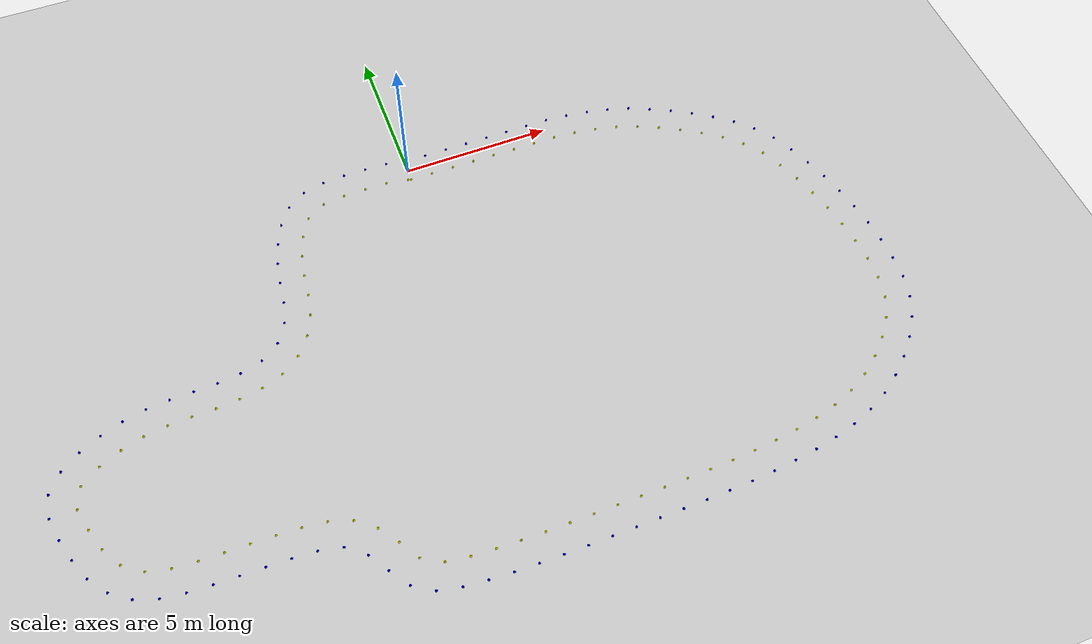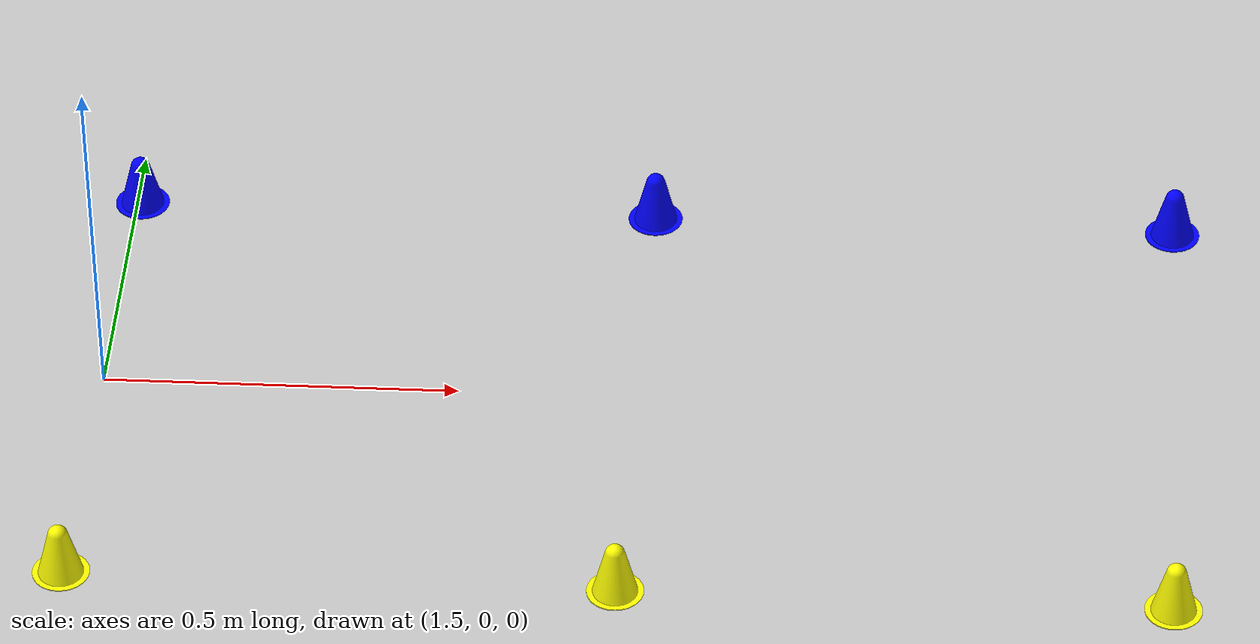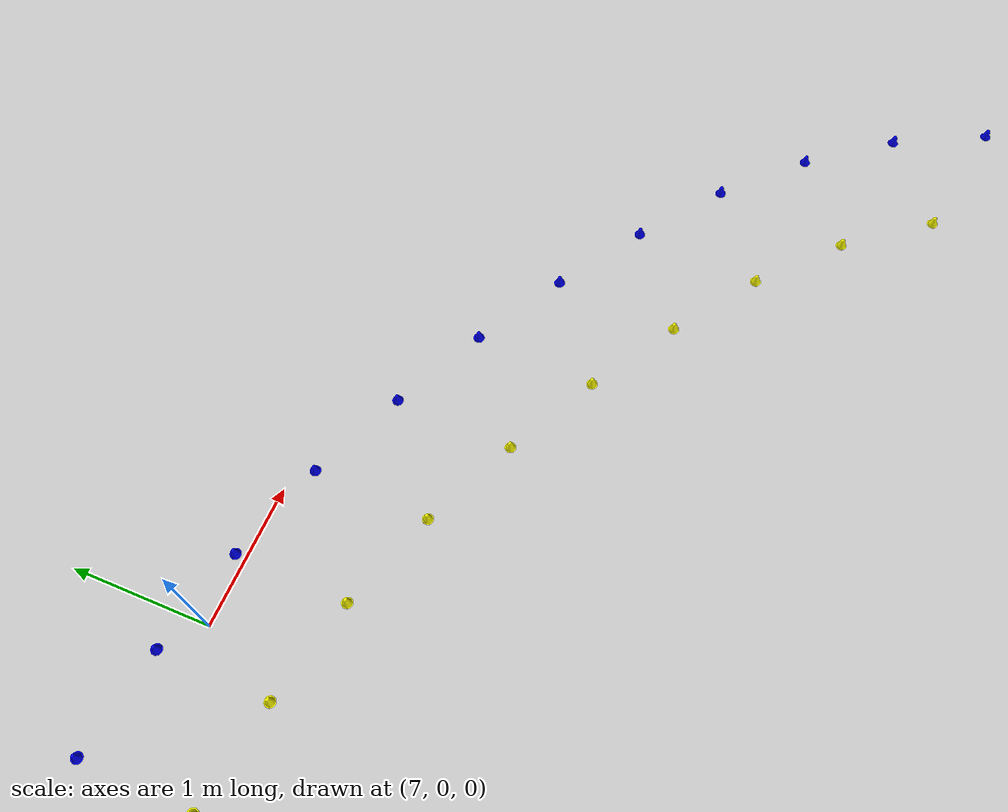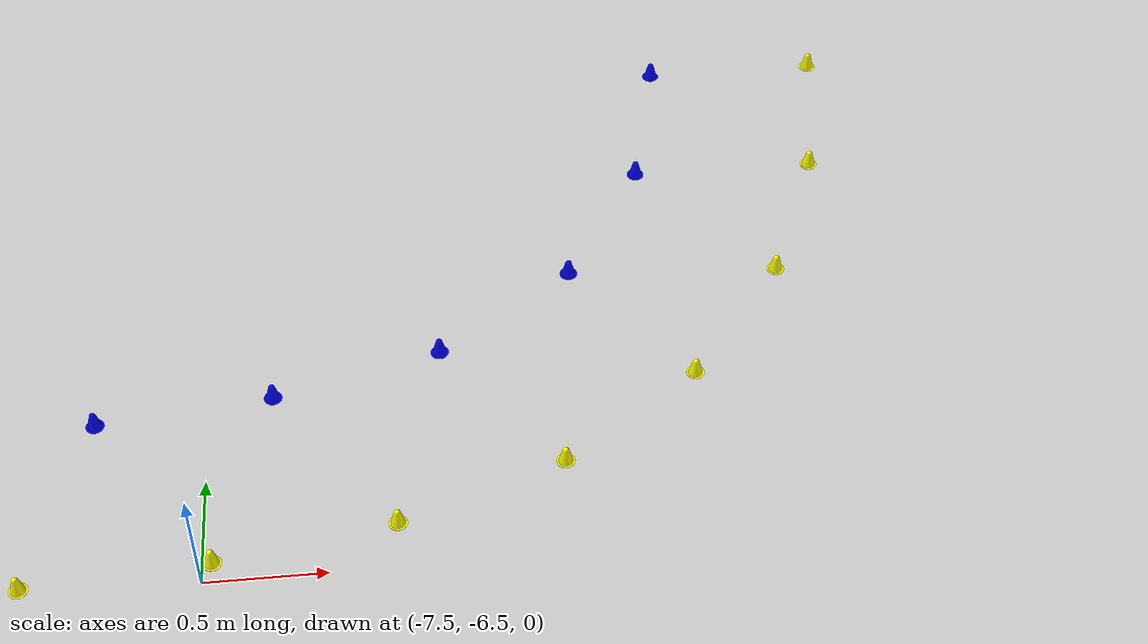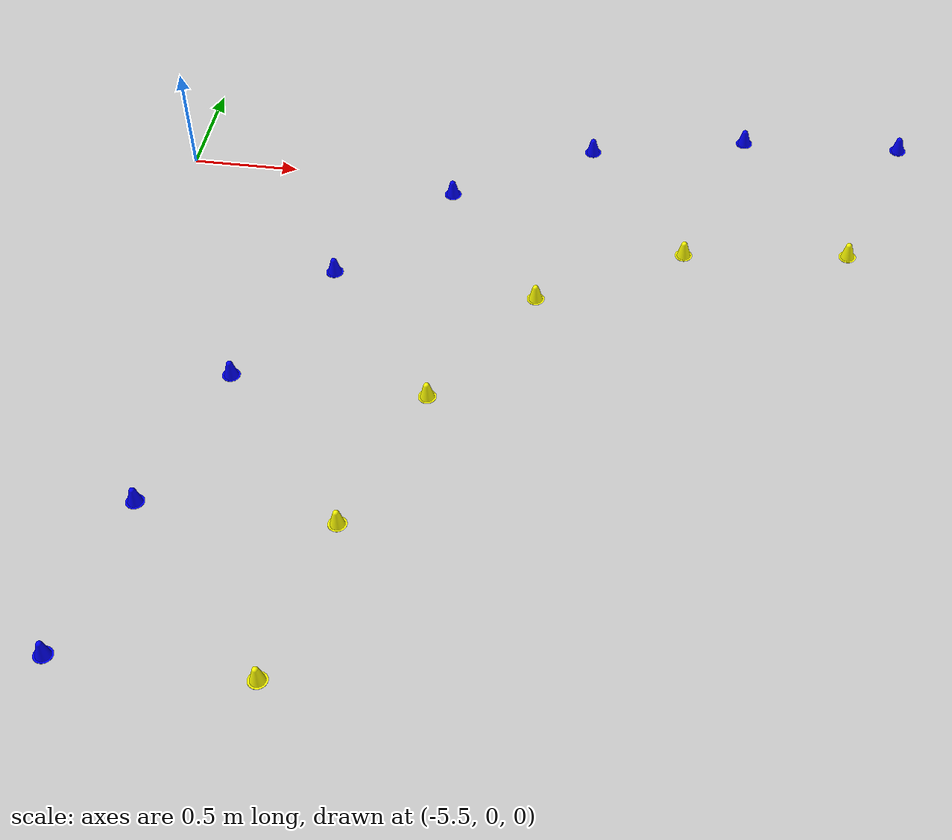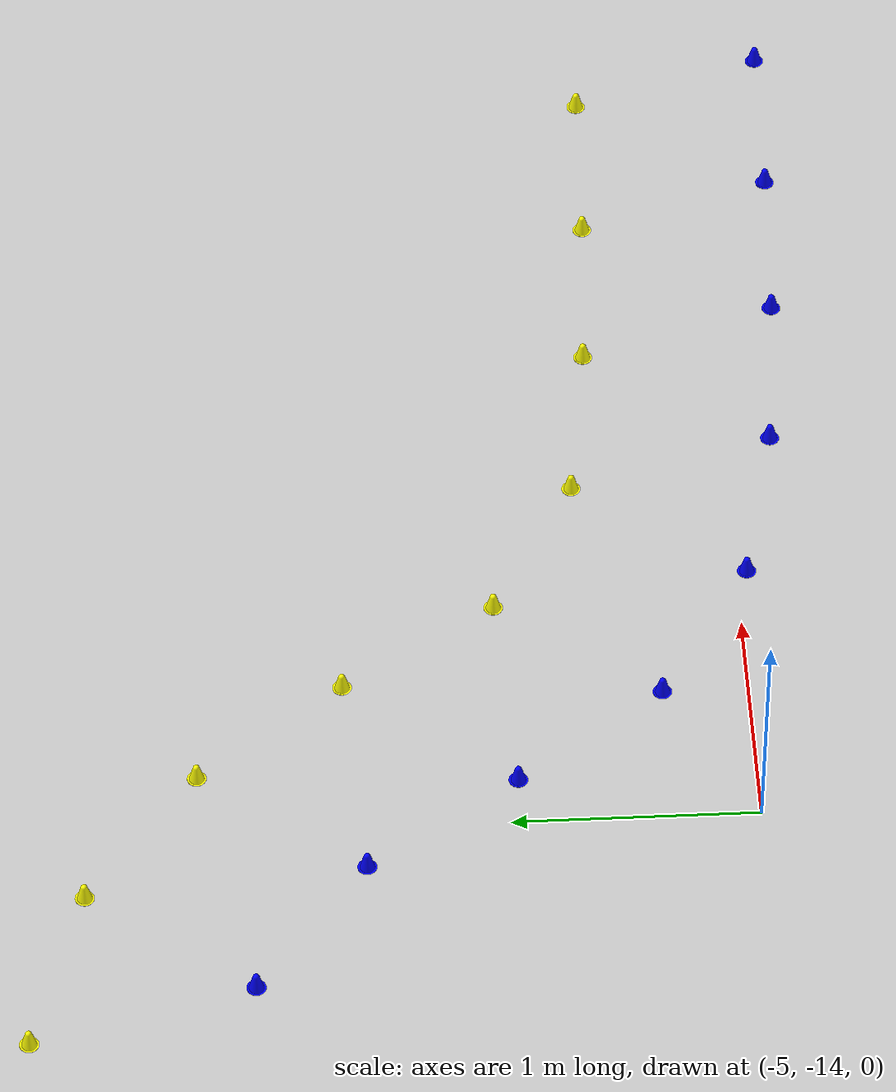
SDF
<?xml version="1.0" ?>
<sdf version="1.7">
  <world name="default">
       <light type="directional" name="sun">
            <cast_shadows>true</cast_shadows>
            <pose>0 0 10 0 0 0</pose>
            <diffuse>0.8 0.8 0.8 1</diffuse>
            <specular>0.2 0.2 0.2 1</specular>
            <attenuation>
                <range>1000</range>
                <constant>0.9</constant>
                <linear>0.01</linear>
                <quadratic>0.001</quadratic>
            </attenuation>
            <direction>-0.5 0.1 -0.9</direction>
        </light>

        <model name="ground_plane">
            <static>true</static>
           <link name="link">
                <collision name="collision">
                    <geometry>
                        <plane>
                            <normal>0 0 1</normal>
                        </plane>
                    </geometry>
                </collision>
                <visual name="visual">
                    <geometry>
                        <plane>
                            <normal>0 0 1</normal>
                            <size>100 100</size>
                        </plane>
                    </geometry>
                    <material>
                        <ambient>0.8 0.8 0.8 1</ambient>
                        <diffuse>0.8 0.8 0.8 1</diffuse>
                        <specular>0.8 0.8 0.8 1</specular>
                    </material>
                </visual>
            </link>
        </model>
    <model name="model_blue_0">
          <pose>-13.508779008248382 -8.209662979512794 0.005 0 0 0</pose>
      <static>true</static>
      <link name="body">
        <visual name="visual">
          <geometry>
            <mesh>
              <uri>model://tamiyabot_description/models/cone_green.stl</uri>
              <scale>0.001 0.001 0.001</scale>
            </mesh>
          </geometry>
          <material>
            <ambient>0.0 0.0 1.0 1.0</ambient>
            <diffuse>0.0 0.0 1.0 1.0</diffuse>
            <specular>0.5 0.5 0.5 1.0</specular>
            <emissive>0.0 0.0 0.0 1.0</emissive>
          </material>
        </visual>
      </link>
    </model>
    <model name="model_blue_1">
          <pose>-13.415422171728364 -7.474735556839779 0.005 0 0 0</pose>
      <static>true</static>
      <link name="body">
        <visual name="visual">
          <geometry>
            <mesh>
              <uri>model://tamiyabot_description/models/cone_green.stl</uri>
              <scale>0.001 0.001 0.001</scale>
            </mesh>
          </geometry>
<material>
            <ambient>0.0 0.0 1.0 1.0</ambient>
            <diffuse>0.0 0.0 1.0 1.0</diffuse>
            <specular>0.5 0.5 0.5 1.0</specular>
            <emissive>0.0 0.0 0.0 1.0</emissive>
          </material>
        </visual>
      </link>
    </model>
    <model name="model_blue_2">
          <pose>-13.340663214534047 -8.939716505920162 0.005 0 0 0</pose>
      <static>true</static>
      <link name="body">
        <visual name="visual">
          <geometry>
            <mesh>
              <uri>model://tamiyabot_description/models/cone_green.stl</uri>
              <scale>0.001 0.001 0.001</scale>
            </mesh>
          </geometry>
<material>
            <ambient>0.0 0.0 1.0 1.0</ambient>
            <diffuse>0.0 0.0 1.0 1.0</diffuse>
            <specular>0.5 0.5 0.5 1.0</specular>
            <emissive>0.0 0.0 0.0 1.0</emissive>
          </material>
        </visual>
      </link>
    </model>
    <model name="model_blue_3">
          <pose>-13.100009412662647 -9.649854828439892 0.005 0 0 0</pose>
      <static>true</static>
      <link name="body">
        <visual name="visual">
          <geometry>
            <mesh>
              <uri>model://tamiyabot_description/models/cone_green.stl</uri>
              <scale>0.001 0.001 0.001</scale>
            </mesh>
          </geometry>
<material>
            <ambient>0.0 0.0 1.0 1.0</ambient>
            <diffuse>0.0 0.0 1.0 1.0</diffuse>
            <specular>0.5 0.5 0.5 1.0</specular>
            <emissive>0.0 0.0 0.0 1.0</emissive>
          </material>
        </visual>
      </link>
    </model>
    <model name="model_blue_4">
          <pose>-12.963956328914604 -6.883579469301832 0.005 0 0 0</pose>
      <static>true</static>
      <link name="body">
        <visual name="visual">
          <geometry>
            <mesh>
              <uri>model://tamiyabot_description/models/cone_green.stl</uri>
              <scale>0.001 0.001 0.001</scale>
            </mesh>
          </geometry>
<material>
            <ambient>0.0 0.0 1.0 1.0</ambient>
            <diffuse>0.0 0.0 1.0 1.0</diffuse>
            <specular>0.5 0.5 0.5 1.0</specular>
            <emissive>0.0 0.0 0.0 1.0</emissive>
          </material>
        </visual>
      </link>
    </model>
    <model name="model_blue_5">
          <pose>-12.786137976061493 -10.330166847527892 0.005 0 0 0</pose>
      <static>true</static>
      <link name="body">
        <visual name="visual">
          <geometry>
            <mesh>
              <uri>model://tamiyabot_description/models/cone_green.stl</uri>
              <scale>0.001 0.001 0.001</scale>
            </mesh>
          </geometry>
<material>
            <ambient>0.0 0.0 1.0 1.0</ambient>
            <diffuse>0.0 0.0 1.0 1.0</diffuse>
            <specular>0.5 0.5 0.5 1.0</specular>
            <emissive>0.0 0.0 0.0 1.0</emissive>
          </material>
        </visual>
      </link>
    </model>
    <model name="model_blue_6">
          <pose>-12.34526358427565 -6.462482057638111 0.005 0 0 0</pose>
      <static>true</static>
      <link name="body">
        <visual name="visual">
          <geometry>
            <mesh>
              <uri>model://tamiyabot_description/models/cone_green.stl</uri>
              <scale>0.001 0.001 0.001</scale>
            </mesh>
          </geometry>
<material>
            <ambient>0.0 0.0 1.0 1.0</ambient>
            <diffuse>0.0 0.0 1.0 1.0</diffuse>
            <specular>0.5 0.5 0.5 1.0</specular>
            <emissive>0.0 0.0 0.0 1.0</emissive>
          </material>
        </visual>
      </link>
    </model>
    <model name="model_blue_7">
          <pose>-12.321278323363424 -10.91516859587372 0.005 0 0 0</pose>
      <static>true</static>
      <link name="body">
        <visual name="visual">
          <geometry>
            <mesh>
              <uri>model://tamiyabot_description/models/cone_green.stl</uri>
              <scale>0.001 0.001 0.001</scale>
            </mesh>
          </geometry>
<material>
            <ambient>0.0 0.0 1.0 1.0</ambient>
            <diffuse>0.0 0.0 1.0 1.0</diffuse>
            <specular>0.5 0.5 0.5 1.0</specular>
            <emissive>0.0 0.0 0.0 1.0</emissive>
          </material>
        </visual>
      </link>
    </model>
    <model name="model_blue_8">
          <pose>-11.709509574359416 -11.34480917467532 0.005 0 0 0</pose>
      <static>true</static>
      <link name="body">
        <visual name="visual">
          <geometry>
            <mesh>
              <uri>model://tamiyabot_description/models/cone_green.stl</uri>
              <scale>0.001 0.001 0.001</scale>
            </mesh>
          </geometry>
<material>
            <ambient>0.0 0.0 1.0 1.0</ambient>
            <diffuse>0.0 0.0 1.0 1.0</diffuse>
            <specular>0.5 0.5 0.5 1.0</specular>
            <emissive>0.0 0.0 0.0 1.0</emissive>
          </material>
        </visual>
      </link>
    </model>
    <model name="model_blue_9">
          <pose>-11.663943830883703 -6.15015339698074 0.005 0 0 0</pose>
      <static>true</static>
      <link name="body">
        <visual name="visual">
          <geometry>
            <mesh>
              <uri>model://tamiyabot_description/models/cone_green.stl</uri>
              <scale>0.001 0.001 0.001</scale>
            </mesh>
          </geometry>
<material>
            <ambient>0.0 0.0 1.0 1.0</ambient>
            <diffuse>0.0 0.0 1.0 1.0</diffuse>
            <specular>0.5 0.5 0.5 1.0</specular>
            <emissive>0.0 0.0 0.0 1.0</emissive>
          </material>
        </visual>
      </link>
    </model>
    <model name="model_blue_10">
          <pose>-11.0015940669735 -11.585273242222975 0.005 0 0 0</pose>
      <static>true</static>
      <link name="body">
        <visual name="visual">
          <geometry>
            <mesh>
              <uri>model://tamiyabot_description/models/cone_green.stl</uri>
              <scale>0.001 0.001 0.001</scale>
            </mesh>
          </geometry>
<material>
            <ambient>0.0 0.0 1.0 1.0</ambient>
            <diffuse>0.0 0.0 1.0 1.0</diffuse>
            <specular>0.5 0.5 0.5 1.0</specular>
            <emissive>0.0 0.0 0.0 1.0</emissive>
          </material>
        </visual>
      </link>
    </model>
    <model name="model_blue_11">
          <pose>-10.952446150445187 -5.914030631136217 0.005 0 0 0</pose>
      <static>true</static>
      <link name="body">
        <visual name="visual">
          <geometry>
            <mesh>
              <uri>model://tamiyabot_description/models/cone_green.stl</uri>
              <scale>0.001 0.001 0.001</scale>
            </mesh>
          </geometry>
<material>
            <ambient>0.0 0.0 1.0 1.0</ambient>
            <diffuse>0.0 0.0 1.0 1.0</diffuse>
            <specular>0.5 0.5 0.5 1.0</specular>
            <emissive>0.0 0.0 0.0 1.0</emissive>
          </material>
        </visual>
      </link>
    </model>
    <model name="model_blue_12">
          <pose>-10.258247181017008 -11.680862146332334 0.005 0 0 0</pose>
      <static>true</static>
      <link name="body">
        <visual name="visual">
          <geometry>
            <mesh>
              <uri>model://tamiyabot_description/models/cone_green.stl</uri>
              <scale>0.001 0.001 0.001</scale>
            </mesh>
          </geometry>
<material>
            <ambient>0.0 0.0 1.0 1.0</ambient>
            <diffuse>0.0 0.0 1.0 1.0</diffuse>
            <specular>0.5 0.5 0.5 1.0</specular>
            <emissive>0.0 0.0 0.0 1.0</emissive>
          </material>
        </visual>
      </link>
    </model>
    <model name="model_blue_13">
          <pose>-10.218026733847564 -5.764783516803635 0.005 0 0 0</pose>
      <static>true</static>
      <link name="body">
        <visual name="visual">
          <geometry>
            <mesh>
              <uri>model://tamiyabot_description/models/cone_green.stl</uri>
              <scale>0.001 0.001 0.001</scale>
            </mesh>
          </geometry>
<material>
            <ambient>0.0 0.0 1.0 1.0</ambient>
            <diffuse>0.0 0.0 1.0 1.0</diffuse>
            <specular>0.5 0.5 0.5 1.0</specular>
            <emissive>0.0 0.0 0.0 1.0</emissive>
          </material>
        </visual>
      </link>
    </model>
    <model name="model_blue_14">
          <pose>-9.509124639590032 -11.715573718884032 0.005 0 0 0</pose>
      <static>true</static>
      <link name="body">
        <visual name="visual">
          <geometry>
            <mesh>
              <uri>model://tamiyabot_description/models/cone_green.stl</uri>
              <scale>0.001 0.001 0.001</scale>
            </mesh>
          </geometry>
<material>
            <ambient>0.0 0.0 1.0 1.0</ambient>
            <diffuse>0.0 0.0 1.0 1.0</diffuse>
            <specular>0.5 0.5 0.5 1.0</specular>
            <emissive>0.0 0.0 0.0 1.0</emissive>
          </material>
        </visual>
      </link>
    </model>
    <model name="model_blue_15">
          <pose>-9.471048430512624 -5.700297145105742 0.005 0 0 0</pose>
      <static>true</static>
      <link name="body">
        <visual name="visual">
          <geometry>
            <mesh>
              <uri>model://tamiyabot_description/models/cone_green.stl</uri>
              <scale>0.001 0.001 0.001</scale>
            </mesh>
          </geometry>
<material>
            <ambient>0.0 0.0 1.0 1.0</ambient>
            <diffuse>0.0 0.0 1.0 1.0</diffuse>
            <specular>0.5 0.5 0.5 1.0</specular>
            <emissive>0.0 0.0 0.0 1.0</emissive>
          </material>
        </visual>
      </link>
    </model>
    <model name="model_blue_16">
          <pose>-8.759240135203864 -11.72822996636487 0.005 0 0 0</pose>
      <static>true</static>
      <link name="body">
        <visual name="visual">
          <geometry>
            <mesh>
              <uri>model://tamiyabot_description/models/cone_green.stl</uri>
              <scale>0.001 0.001 0.001</scale>
            </mesh>
          </geometry>
<material>
            <ambient>0.0 0.0 1.0 1.0</ambient>
            <diffuse>0.0 0.0 1.0 1.0</diffuse>
            <specular>0.5 0.5 0.5 1.0</specular>
            <emissive>0.0 0.0 0.0 1.0</emissive>
          </material>
        </visual>
      </link>
    </model>
    <model name="model_blue_17">
          <pose>-8.721328365268597 -5.681330476365732 0.005 0 0 0</pose>
      <static>true</static>
      <link name="body">
        <visual name="visual">
          <geometry>
            <mesh>
              <uri>model://tamiyabot_description/models/cone_green.stl</uri>
              <scale>0.001 0.001 0.001</scale>
            </mesh>
          </geometry>
<material>
            <ambient>0.0 0.0 1.0 1.0</ambient>
            <diffuse>0.0 0.0 1.0 1.0</diffuse>
            <specular>0.5 0.5 0.5 1.0</specular>
            <emissive>0.0 0.0 0.0 1.0</emissive>
          </material>
        </visual>
      </link>
    </model>
    <model name="model_blue_18">
          <pose>-8.009281872598226 -11.736108235214113 0.005 0 0 0</pose>
      <static>true</static>
      <link name="body">
        <visual name="visual">
          <geometry>
            <mesh>
              <uri>model://tamiyabot_description/models/cone_green.stl</uri>
              <scale>0.001 0.001 0.001</scale>
            </mesh>
          </geometry>
<material>
            <ambient>0.0 0.0 1.0 1.0</ambient>
            <diffuse>0.0 0.0 1.0 1.0</diffuse>
            <specular>0.5 0.5 0.5 1.0</specular>
            <emissive>0.0 0.0 0.0 1.0</emissive>
          </material>
        </visual>
      </link>
    </model>
    <model name="model_blue_19">
          <pose>-7.971839628186241 -5.657042748141666 0.005 0 0 0</pose>
      <static>true</static>
      <link name="body">
        <visual name="visual">
          <geometry>
            <mesh>
              <uri>model://tamiyabot_description/models/cone_green.stl</uri>
              <scale>0.001 0.001 0.001</scale>
            </mesh>
          </geometry>
<material>
            <ambient>0.0 0.0 1.0 1.0</ambient>
            <diffuse>0.0 0.0 1.0 1.0</diffuse>
            <specular>0.5 0.5 0.5 1.0</specular>
            <emissive>0.0 0.0 0.0 1.0</emissive>
          </material>
        </visual>
      </link>
    </model>
    <model name="model_blue_20">
          <pose>-7.259504207578555 -11.753582872394734 0.005 0 0 0</pose>
      <static>true</static>
      <link name="body">
        <visual name="visual">
          <geometry>
            <mesh>
              <uri>model://tamiyabot_description/models/cone_green.stl</uri>
              <scale>0.001 0.001 0.001</scale>
            </mesh>
          </geometry>
<material>
            <ambient>0.0 0.0 1.0 1.0</ambient>
            <diffuse>0.0 0.0 1.0 1.0</diffuse>
            <specular>0.5 0.5 0.5 1.0</specular>
            <emissive>0.0 0.0 0.0 1.0</emissive>
          </material>
        </visual>
      </link>
    </model>
    <model name="model_blue_21">
          <pose>-7.227051978788251 -5.571191484504595 0.005 0 0 0</pose>
      <static>true</static>
      <link name="body">
        <visual name="visual">
          <geometry>
            <mesh>
              <uri>model://tamiyabot_description/models/cone_green.stl</uri>
              <scale>0.001 0.001 0.001</scale>
            </mesh>
          </geometry>
<material>
            <ambient>0.0 0.0 1.0 1.0</ambient>
            <diffuse>0.0 0.0 1.0 1.0</diffuse>
            <specular>0.5 0.5 0.5 1.0</specular>
            <emissive>0.0 0.0 0.0 1.0</emissive>
          </material>
        </visual>
      </link>
    </model>
    <model name="model_blue_22">
          <pose>-6.511362149036095 -11.804119751062526 0.005 0 0 0</pose>
      <static>true</static>
      <link name="body">
        <visual name="visual">
          <geometry>
            <mesh>
              <uri>model://tamiyabot_description/models/cone_green.stl</uri>
              <scale>0.001 0.001 0.001</scale>
            </mesh>
          </geometry>
<material>
            <ambient>0.0 0.0 1.0 1.0</ambient>
            <diffuse>0.0 0.0 1.0 1.0</diffuse>
            <specular>0.5 0.5 0.5 1.0</specular>
            <emissive>0.0 0.0 0.0 1.0</emissive>
          </material>
        </visual>
      </link>
    </model>
    <model name="model_blue_23">
          <pose>-6.504548647682264 -5.376818406440758 0.005 0 0 0</pose>
      <static>true</static>
      <link name="body">
        <visual name="visual">
          <geometry>
            <mesh>
              <uri>model://tamiyabot_description/models/cone_green.stl</uri>
              <scale>0.001 0.001 0.001</scale>
            </mesh>
          </geometry>
<material>
            <ambient>0.0 0.0 1.0 1.0</ambient>
            <diffuse>0.0 0.0 1.0 1.0</diffuse>
            <specular>0.5 0.5 0.5 1.0</specular>
            <emissive>0.0 0.0 0.0 1.0</emissive>
          </material>
        </visual>
      </link>
    </model>
    <model name="model_blue_24">
          <pose>-5.894388042275276 -4.950474163996766 0.005 0 0 0</pose>
      <static>true</static>
      <link name="body">
        <visual name="visual">
          <geometry>
            <mesh>
              <uri>model://tamiyabot_description/models/cone_green.stl</uri>
              <scale>0.001 0.001 0.001</scale>
            </mesh>
          </geometry>
<material>
            <ambient>0.0 0.0 1.0 1.0</ambient>
            <diffuse>0.0 0.0 1.0 1.0</diffuse>
            <specular>0.5 0.5 0.5 1.0</specular>
            <emissive>0.0 0.0 0.0 1.0</emissive>
          </material>
        </visual>
      </link>
    </model>
    <model name="model_blue_25">
          <pose>-5.779253173799928 -11.957744176947324 0.005 0 0 0</pose>
      <static>true</static>
      <link name="body">
        <visual name="visual">
          <geometry>
            <mesh>
              <uri>model://tamiyabot_description/models/cone_green.stl</uri>
              <scale>0.001 0.001 0.001</scale>
            </mesh>
          </geometry>
<material>
            <ambient>0.0 0.0 1.0 1.0</ambient>
            <diffuse>0.0 0.0 1.0 1.0</diffuse>
            <specular>0.5 0.5 0.5 1.0</specular>
            <emissive>0.0 0.0 0.0 1.0</emissive>
          </material>
        </visual>
      </link>
    </model>
    <model name="model_blue_26">
          <pose>-5.504484478113237 -4.315204554487792 0.005 0 0 0</pose>
      <static>true</static>
      <link name="body">
        <visual name="visual">
          <geometry>
            <mesh>
              <uri>model://tamiyabot_description/models/cone_green.stl</uri>
              <scale>0.001 0.001 0.001</scale>
            </mesh>
          </geometry>
<material>
            <ambient>0.0 0.0 1.0 1.0</ambient>
            <diffuse>0.0 0.0 1.0 1.0</diffuse>
            <specular>0.5 0.5 0.5 1.0</specular>
            <emissive>0.0 0.0 0.0 1.0</emissive>
          </material>
        </visual>
      </link>
    </model>
    <model name="model_blue_27">
          <pose>-5.33118987103772 -3.5874641089163526 0.005 0 0 0</pose>
      <static>true</static>
      <link name="body">
        <visual name="visual">
          <geometry>
            <mesh>
              <uri>model://tamiyabot_description/models/cone_green.stl</uri>
              <scale>0.001 0.001 0.001</scale>
            </mesh>
          </geometry>
<material>
            <ambient>0.0 0.0 1.0 1.0</ambient>
            <diffuse>0.0 0.0 1.0 1.0</diffuse>
            <specular>0.5 0.5 0.5 1.0</specular>
            <emissive>0.0 0.0 0.0 1.0</emissive>
          </material>
        </visual>
      </link>
    </model>
    <model name="model_blue_28">
          <pose>-5.255683617391744 -2.8413118118163077 0.005 0 0 0</pose>
      <static>true</static>
      <link name="body">
        <visual name="visual">
          <geometry>
            <mesh>
              <uri>model://tamiyabot_description/models/cone_green.stl</uri>
              <scale>0.001 0.001 0.001</scale>
            </mesh>
          </geometry>
<material>
            <ambient>0.0 0.0 1.0 1.0</ambient>
            <diffuse>0.0 0.0 1.0 1.0</diffuse>
            <specular>0.5 0.5 0.5 1.0</specular>
            <emissive>0.0 0.0 0.0 1.0</emissive>
          </material>
        </visual>
      </link>
    </model>
    <model name="model_blue_29">
          <pose>-5.198951000833129 -12.41604838219067 0.005 0 0 0</pose>
      <static>true</static>
      <link name="body">
        <visual name="visual">
          <geometry>
            <mesh>
              <uri>model://tamiyabot_description/models/cone_green.stl</uri>
              <scale>0.001 0.001 0.001</scale>
            </mesh>
          </geometry>
<material>
            <ambient>0.0 0.0 1.0 1.0</ambient>
            <diffuse>0.0 0.0 1.0 1.0</diffuse>
            <specular>0.5 0.5 0.5 1.0</specular>
            <emissive>0.0 0.0 0.0 1.0</emissive>
          </material>
        </visual>
      </link>
    </model>
    <model name="model_blue_30">
          <pose>-5.142164498209789 -2.1002762891282596 0.005 0 0 0</pose>
      <static>true</static>
      <link name="body">
        <visual name="visual">
          <geometry>
            <mesh>
              <uri>model://tamiyabot_description/models/cone_green.stl</uri>
              <scale>0.001 0.001 0.001</scale>
            </mesh>
          </geometry>
<material>
            <ambient>0.0 0.0 1.0 1.0</ambient>
            <diffuse>0.0 0.0 1.0 1.0</diffuse>
            <specular>0.5 0.5 0.5 1.0</specular>
            <emissive>0.0 0.0 0.0 1.0</emissive>
          </material>
        </visual>
      </link>
    </model>
    <model name="model_blue_31">
          <pose>-4.947103064859367 -1.3765516928474204 0.005 0 0 0</pose>
      <static>true</static>
      <link name="body">
        <visual name="visual">
          <geometry>
            <mesh>
              <uri>model://tamiyabot_description/models/cone_green.stl</uri>
              <scale>0.001 0.001 0.001</scale>
            </mesh>
          </geometry>
<material>
            <ambient>0.0 0.0 1.0 1.0</ambient>
            <diffuse>0.0 0.0 1.0 1.0</diffuse>
            <specular>0.5 0.5 0.5 1.0</specular>
            <emissive>0.0 0.0 0.0 1.0</emissive>
          </material>
        </visual>
      </link>
    </model>
    <model name="model_blue_32">
          <pose>-4.7834950119586646 -13.03975138490879 0.005 0 0 0</pose>
      <static>true</static>
      <link name="body">
        <visual name="visual">
          <geometry>
            <mesh>
              <uri>model://tamiyabot_description/models/cone_green.stl</uri>
              <scale>0.001 0.001 0.001</scale>
            </mesh>
          </geometry>
<material>
            <ambient>0.0 0.0 1.0 1.0</ambient>
            <diffuse>0.0 0.0 1.0 1.0</diffuse>
            <specular>0.5 0.5 0.5 1.0</specular>
            <emissive>0.0 0.0 0.0 1.0</emissive>
          </material>
        </visual>
      </link>
    </model>
    <model name="model_blue_33">
          <pose>-4.652975967576984 -0.6876671162762047 0.005 0 0 0</pose>
      <static>true</static>
      <link name="body">
        <visual name="visual">
          <geometry>
            <mesh>
              <uri>model://tamiyabot_description/models/cone_green.stl</uri>
              <scale>0.001 0.001 0.001</scale>
            </mesh>
          </geometry>
<material>
            <ambient>0.0 0.0 1.0 1.0</ambient>
            <diffuse>0.0 0.0 1.0 1.0</diffuse>
            <specular>0.5 0.5 0.5 1.0</specular>
            <emissive>0.0 0.0 0.0 1.0</emissive>
          </material>
        </visual>
      </link>
    </model>
    <model name="model_blue_34">
          <pose>-4.350983110779053 -13.64955791491227 0.005 0 0 0</pose>
      <static>true</static>
      <link name="body">
        <visual name="visual">
          <geometry>
            <mesh>
              <uri>model://tamiyabot_description/models/cone_green.stl</uri>
              <scale>0.001 0.001 0.001</scale>
            </mesh>
          </geometry>
<material>
            <ambient>0.0 0.0 1.0 1.0</ambient>
            <diffuse>0.0 0.0 1.0 1.0</diffuse>
            <specular>0.5 0.5 0.5 1.0</specular>
            <emissive>0.0 0.0 0.0 1.0</emissive>
          </material>
        </visual>
      </link>
    </model>
    <model name="model_blue_35">
          <pose>-4.214628303895624 -0.0820797703572527 0.005 0 0 0</pose>
      <static>true</static>
      <link name="body">
        <visual name="visual">
          <geometry>
            <mesh>
              <uri>model://tamiyabot_description/models/cone_green.stl</uri>
              <scale>0.001 0.001 0.001</scale>
            </mesh>
          </geometry>
<material>
            <ambient>0.0 0.0 1.0 1.0</ambient>
            <diffuse>0.0 0.0 1.0 1.0</diffuse>
            <specular>0.5 0.5 0.5 1.0</specular>
            <emissive>0.0 0.0 0.0 1.0</emissive>
          </material>
        </visual>
      </link>
    </model>
    <model name="model_blue_36">
          <pose>-3.719841168838687 -14.042888404421314 0.005 0 0 0</pose>
      <static>true</static>
      <link name="body">
        <visual name="visual">
          <geometry>
            <mesh>
              <uri>model://tamiyabot_description/models/cone_green.stl</uri>
              <scale>0.001 0.001 0.001</scale>
            </mesh>
          </geometry>
<material>
            <ambient>0.0 0.0 1.0 1.0</ambient>
            <diffuse>0.0 0.0 1.0 1.0</diffuse>
            <specular>0.5 0.5 0.5 1.0</specular>
            <emissive>0.0 0.0 0.0 1.0</emissive>
          </material>
        </visual>
      </link>
    </model>
    <model name="model_blue_37">
          <pose>-3.590523477653215 0.32341492618642326 0.005 0 0 0</pose>
      <static>true</static>
      <link name="body">
        <visual name="visual">
          <geometry>
            <mesh>
              <uri>model://tamiyabot_description/models/cone_green.stl</uri>
              <scale>0.001 0.001 0.001</scale>
            </mesh>
          </geometry>
<material>
            <ambient>0.0 0.0 1.0 1.0</ambient>
            <diffuse>0.0 0.0 1.0 1.0</diffuse>
            <specular>0.5 0.5 0.5 1.0</specular>
            <emissive>0.0 0.0 0.0 1.0</emissive>
          </material>
        </visual>
      </link>
    </model>
    <model name="model_blue_38">
          <pose>-2.9877207368708008 -14.199052728824242 0.005 0 0 0</pose>
      <static>true</static>
      <link name="body">
        <visual name="visual">
          <geometry>
            <mesh>
              <uri>model://tamiyabot_description/models/cone_green.stl</uri>
              <scale>0.001 0.001 0.001</scale>
            </mesh>
          </geometry>
<material>
            <ambient>0.0 0.0 1.0 1.0</ambient>
            <diffuse>0.0 0.0 1.0 1.0</diffuse>
            <specular>0.5 0.5 0.5 1.0</specular>
            <emissive>0.0 0.0 0.0 1.0</emissive>
          </material>
        </visual>
      </link>
    </model>
    <model name="model_blue_39">
          <pose>-2.8624959240493664 0.49567361733275 0.005 0 0 0</pose>
      <static>true</static>
      <link name="body">
        <visual name="visual">
          <geometry>
            <mesh>
              <uri>model://tamiyabot_description/models/cone_green.stl</uri>
              <scale>0.001 0.001 0.001</scale>
            </mesh>
          </geometry>
<material>
            <ambient>0.0 0.0 1.0 1.0</ambient>
            <diffuse>0.0 0.0 1.0 1.0</diffuse>
            <specular>0.5 0.5 0.5 1.0</specular>
            <emissive>0.0 0.0 0.0 1.0</emissive>
          </material>
        </visual>
      </link>
    </model>
    <model name="model_blue_40">
          <pose>-2.2409240862587634 -14.26689367318963 0.005 0 0 0</pose>
      <static>true</static>
      <link name="body">
        <visual name="visual">
          <geometry>
            <mesh>
              <uri>model://tamiyabot_description/models/cone_green.stl</uri>
              <scale>0.001 0.001 0.001</scale>
            </mesh>
          </geometry>
<material>
            <ambient>0.0 0.0 1.0 1.0</ambient>
            <diffuse>0.0 0.0 1.0 1.0</diffuse>
            <specular>0.5 0.5 0.5 1.0</specular>
            <emissive>0.0 0.0 0.0 1.0</emissive>
          </material>
        </visual>
      </link>
    </model>
    <model name="model_blue_41">
          <pose>-2.114309626268659 0.5418417626528416 0.005 0 0 0</pose>
      <static>true</static>
      <link name="body">
        <visual name="visual">
          <geometry>
            <mesh>
              <uri>model://tamiyabot_description/models/cone_green.stl</uri>
              <scale>0.001 0.001 0.001</scale>
            </mesh>
          </geometry>
<material>
            <ambient>0.0 0.0 1.0 1.0</ambient>
            <diffuse>0.0 0.0 1.0 1.0</diffuse>
            <specular>0.5 0.5 0.5 1.0</specular>
            <emissive>0.0 0.0 0.0 1.0</emissive>
          </material>
        </visual>
      </link>
    </model>
    <model name="model_blue_42">
          <pose>-1.4917437086213523 -14.301246618904175 0.005 0 0 0</pose>
      <static>true</static>
      <link name="body">
        <visual name="visual">
          <geometry>
            <mesh>
              <uri>model://tamiyabot_description/models/cone_green.stl</uri>
              <scale>0.001 0.001 0.001</scale>
            </mesh>
          </geometry>
<material>
            <ambient>0.0 0.0 1.0 1.0</ambient>
            <diffuse>0.0 0.0 1.0 1.0</diffuse>
            <specular>0.5 0.5 0.5 1.0</specular>
            <emissive>0.0 0.0 0.0 1.0</emissive>
          </material>
        </visual>
      </link>
    </model>
    <model name="model_blue_43">
          <pose>-1.3643204635551307 0.5443772182764302 0.005 0 0 0</pose>
      <static>true</static>
      <link name="body">
        <visual name="visual">
          <geometry>
            <mesh>
              <uri>model://tamiyabot_description/models/cone_green.stl</uri>
              <scale>0.001 0.001 0.001</scale>
            </mesh>
          </geometry>
<material>
            <ambient>0.0 0.0 1.0 1.0</ambient>
            <diffuse>0.0 0.0 1.0 1.0</diffuse>
            <specular>0.5 0.5 0.5 1.0</specular>
            <emissive>0.0 0.0 0.0 1.0</emissive>
          </material>
        </visual>
      </link>
    </model>
    <model name="model_blue_44">
          <pose>-0.7419226089679051 -14.3169992112548 0.005 0 0 0</pose>
      <static>true</static>
      <link name="body">
        <visual name="visual">
          <geometry>
            <mesh>
              <uri>model://tamiyabot_description/models/cone_green.stl</uri>
              <scale>0.001 0.001 0.001</scale>
            </mesh>
          </geometry>
<material>
            <ambient>0.0 0.0 1.0 1.0</ambient>
            <diffuse>0.0 0.0 1.0 1.0</diffuse>
            <specular>0.5 0.5 0.5 1.0</specular>
            <emissive>0.0 0.0 0.0 1.0</emissive>
          </material>
        </visual>
      </link>
    </model>
    <model name="model_blue_45">
          <pose>-0.6162093830030027 0.5221592362884409 0.005 0 0 0</pose>
      <static>true</static>
      <link name="body">
        <visual name="visual">
          <geometry>
            <mesh>
              <uri>model://tamiyabot_description/models/cone_green.stl</uri>
              <scale>0.001 0.001 0.001</scale>
            </mesh>
          </geometry>
<material>
            <ambient>0.0 0.0 1.0 1.0</ambient>
            <diffuse>0.0 0.0 1.0 1.0</diffuse>
            <specular>0.5 0.5 0.5 1.0</specular>
            <emissive>0.0 0.0 0.0 1.0</emissive>
          </material>
        </visual>
      </link>
    </model>
    <model name="model_blue_46">
          <pose>0.008061915924190588 -14.320803923377918 0.005 0 0 0</pose>
      <static>true</static>
      <link name="body">
        <visual name="visual">
          <geometry>
            <mesh>
              <uri>model://tamiyabot_description/models/cone_green.stl</uri>
              <scale>0.001 0.001 0.001</scale>
            </mesh>
          </geometry>
<material>
            <ambient>0.0 0.0 1.0 1.0</ambient>
            <diffuse>0.0 0.0 1.0 1.0</diffuse>
            <specular>0.5 0.5 0.5 1.0</specular>
            <emissive>0.0 0.0 0.0 1.0</emissive>
          </material>
        </visual>
      </link>
    </model>
    <model name="model_blue_47">
          <pose>0.008093388369056782 0.39991811294902313 0.005 0 0 0</pose>
      <static>true</static>
      <link name="body">
        <visual name="visual">
          <geometry>
            <mesh>
              <uri>model://tamiyabot_description/models/cone_green.stl</uri>
              <scale>0.001 0.001 0.001</scale>
            </mesh>
          </geometry>
<material>
            <ambient>0.0 0.0 1.0 1.0</ambient>
            <diffuse>0.0 0.0 1.0 1.0</diffuse>
            <specular>0.5 0.5 0.5 1.0</specular>
            <emissive>0.0 0.0 0.0 1.0</emissive>
          </material>
        </visual>
      </link>
    </model>
    <model name="model_blue_48">
          <pose>0.7580487290614314 -14.316750270072033 0.005 0 0 0</pose>
      <static>true</static>
      <link name="body">
        <visual name="visual">
          <geometry>
            <mesh>
              <uri>model://tamiyabot_description/models/cone_green.stl</uri>
              <scale>0.001 0.001 0.001</scale>
            </mesh>
          </geometry>
<material>
            <ambient>0.0 0.0 1.0 1.0</ambient>
            <diffuse>0.0 0.0 1.0 1.0</diffuse>
            <specular>0.5 0.5 0.5 1.0</specular>
            <emissive>0.0 0.0 0.0 1.0</emissive>
          </material>
        </visual>
      </link>
    </model>
    <model name="model_blue_49">
          <pose>0.7580608070985524 0.39446554565609593 0.005 0 0 0</pose>
      <static>true</static>
      <link name="body">
        <visual name="visual">
          <geometry>
            <mesh>
              <uri>model://tamiyabot_description/models/cone_green.stl</uri>
              <scale>0.001 0.001 0.001</scale>
            </mesh>
          </geometry>
<material>
            <ambient>0.0 0.0 1.0 1.0</ambient>
            <diffuse>0.0 0.0 1.0 1.0</diffuse>
            <specular>0.5 0.5 0.5 1.0</specular>
            <emissive>0.0 0.0 0.0 1.0</emissive>
          </material>
        </visual>
      </link>
    </model>
    <model name="model_blue_50">
          <pose>1.5079976180030354 -14.308044149979708 0.005 0 0 0</pose>
      <static>true</static>
      <link name="body">
        <visual name="visual">
          <geometry>
            <mesh>
              <uri>model://tamiyabot_description/models/cone_green.stl</uri>
              <scale>0.001 0.001 0.001</scale>
            </mesh>
          </geometry>
<material>
            <ambient>0.0 0.0 1.0 1.0</ambient>
            <diffuse>0.0 0.0 1.0 1.0</diffuse>
            <specular>0.5 0.5 0.5 1.0</specular>
            <emissive>0.0 0.0 0.0 1.0</emissive>
          </material>
        </visual>
      </link>
    </model>
    <model name="model_blue_51">
          <pose>1.5080607937210242 0.394386479714275 0.005 0 0 0</pose>
      <static>true</static>
      <link name="body">
        <visual name="visual">
          <geometry>
            <mesh>
              <uri>model://tamiyabot_description/models/cone_green.stl</uri>
              <scale>0.001 0.001 0.001</scale>
            </mesh>
          </geometry>
<material>
            <ambient>0.0 0.0 1.0 1.0</ambient>
            <diffuse>0.0 0.0 1.0 1.0</diffuse>
            <specular>0.5 0.5 0.5 1.0</specular>
            <emissive>0.0 0.0 0.0 1.0</emissive>
          </material>
        </visual>
      </link>
    </model>
    <model name="model_blue_52">
          <pose>2.2579249832923107 -14.297608174753451 0.005 0 0 0</pose>
      <static>true</static>
      <link name="body">
        <visual name="visual">
          <geometry>
            <mesh>
              <uri>model://tamiyabot_description/models/cone_green.stl</uri>
              <scale>0.001 0.001 0.001</scale>
            </mesh>
          </geometry>
<material>
            <ambient>0.0 0.0 1.0 1.0</ambient>
            <diffuse>0.0 0.0 1.0 1.0</diffuse>
            <specular>0.5 0.5 0.5 1.0</specular>
            <emissive>0.0 0.0 0.0 1.0</emissive>
          </material>
        </visual>
      </link>
    </model>
    <model name="model_blue_53">
          <pose>2.2580607937210244 0.394386479714275 0.005 0 0 0</pose>
      <static>true</static>
      <link name="body">
        <visual name="visual">
          <geometry>
            <mesh>
              <uri>model://tamiyabot_description/models/cone_green.stl</uri>
              <scale>0.001 0.001 0.001</scale>
            </mesh>
          </geometry>
<material>
            <ambient>0.0 0.0 1.0 1.0</ambient>
            <diffuse>0.0 0.0 1.0 1.0</diffuse>
            <specular>0.5 0.5 0.5 1.0</specular>
            <emissive>0.0 0.0 0.0 1.0</emissive>
          </material>
        </visual>
      </link>
    </model>
    <model name="model_blue_54">
          <pose>3.0078533519729187 -14.287243287500253 0.005 0 0 0</pose>
      <static>true</static>
      <link name="body">
        <visual name="visual">
          <geometry>
            <mesh>
              <uri>model://tamiyabot_description/models/cone_green.stl</uri>
              <scale>0.001 0.001 0.001</scale>
            </mesh>
          </geometry>
<material>
            <ambient>0.0 0.0 1.0 1.0</ambient>
            <diffuse>0.0 0.0 1.0 1.0</diffuse>
            <specular>0.5 0.5 0.5 1.0</specular>
            <emissive>0.0 0.0 0.0 1.0</emissive>
          </material>
        </visual>
      </link>
    </model>
    <model name="model_blue_55">
          <pose>3.0080607937210244 0.394386479714275 0.005 0 0 0</pose>
      <static>true</static>
      <link name="body">
        <visual name="visual">
          <geometry>
            <mesh>
              <uri>model://tamiyabot_description/models/cone_green.stl</uri>
              <scale>0.001 0.001 0.001</scale>
            </mesh>
          </geometry>
<material>
            <ambient>0.0 0.0 1.0 1.0</ambient>
            <diffuse>0.0 0.0 1.0 1.0</diffuse>
            <specular>0.5 0.5 0.5 1.0</specular>
            <emissive>0.0 0.0 0.0 1.0</emissive>
          </material>
        </visual>
      </link>
    </model>
    <model name="model_blue_56">
          <pose>3.7577762213043164 -14.276497674531756 0.005 0 0 0</pose>
      <static>true</static>
      <link name="body">
        <visual name="visual">
          <geometry>
            <mesh>
              <uri>model://tamiyabot_description/models/cone_green.stl</uri>
              <scale>0.001 0.001 0.001</scale>
            </mesh>
          </geometry>
<material>
            <ambient>0.0 0.0 1.0 1.0</ambient>
            <diffuse>0.0 0.0 1.0 1.0</diffuse>
            <specular>0.5 0.5 0.5 1.0</specular>
            <emissive>0.0 0.0 0.0 1.0</emissive>
          </material>
        </visual>
      </link>
    </model>
    <model name="model_blue_57">
          <pose>3.758060793721024 0.394386479714275 0.005 0 0 0</pose>
      <static>true</static>
      <link name="body">
        <visual name="visual">
          <geometry>
            <mesh>
              <uri>model://tamiyabot_description/models/cone_green.stl</uri>
              <scale>0.001 0.001 0.001</scale>
            </mesh>
          </geometry>
<material>
            <ambient>0.0 0.0 1.0 1.0</ambient>
            <diffuse>0.0 0.0 1.0 1.0</diffuse>
            <specular>0.5 0.5 0.5 1.0</specular>
            <emissive>0.0 0.0 0.0 1.0</emissive>
          </material>
        </visual>
      </link>
    </model>
    <model name="model_blue_58">
          <pose>4.507637072673019 -14.262160511455434 0.005 0 0 0</pose>
      <static>true</static>
      <link name="body">
        <visual name="visual">
          <geometry>
            <mesh>
              <uri>model://tamiyabot_description/models/cone_green.stl</uri>
              <scale>0.001 0.001 0.001</scale>
            </mesh>
          </geometry>
<material>
            <ambient>0.0 0.0 1.0 1.0</ambient>
            <diffuse>0.0 0.0 1.0 1.0</diffuse>
            <specular>0.5 0.5 0.5 1.0</specular>
            <emissive>0.0 0.0 0.0 1.0</emissive>
          </material>
        </visual>
      </link>
    </model>
    <model name="model_blue_59">
          <pose>4.508060793441008 0.39437755797965096 0.005 0 0 0</pose>
      <static>true</static>
      <link name="body">
        <visual name="visual">
          <geometry>
            <mesh>
              <uri>model://tamiyabot_description/models/cone_green.stl</uri>
              <scale>0.001 0.001 0.001</scale>
            </mesh>
          </geometry>
<material>
            <ambient>0.0 0.0 1.0 1.0</ambient>
            <diffuse>0.0 0.0 1.0 1.0</diffuse>
            <specular>0.5 0.5 0.5 1.0</specular>
            <emissive>0.0 0.0 0.0 1.0</emissive>
          </material>
        </visual>
      </link>
    </model>
    <model name="model_blue_60">
          <pose>5.257281965759549 -14.239338498933247 0.005 0 0 0</pose>
      <static>true</static>
      <link name="body">
        <visual name="visual">
          <geometry>
            <mesh>
              <uri>model://tamiyabot_description/models/cone_green.stl</uri>
              <scale>0.001 0.001 0.001</scale>
            </mesh>
          </geometry>
<material>
            <ambient>0.0 0.0 1.0 1.0</ambient>
            <diffuse>0.0 0.0 1.0 1.0</diffuse>
            <specular>0.5 0.5 0.5 1.0</specular>
            <emissive>0.0 0.0 0.0 1.0</emissive>
          </material>
        </visual>
      </link>
    </model>
    <model name="model_blue_61">
          <pose>5.258015927496019 0.3889672356973374 0.005 0 0 0</pose>
      <static>true</static>
      <link name="body">
        <visual name="visual">
          <geometry>
            <mesh>
              <uri>model://tamiyabot_description/models/cone_green.stl</uri>
              <scale>0.001 0.001 0.001</scale>
            </mesh>
          </geometry>
<material>
            <ambient>0.0 0.0 1.0 1.0</ambient>
            <diffuse>0.0 0.0 1.0 1.0</diffuse>
            <specular>0.5 0.5 0.5 1.0</specular>
            <emissive>0.0 0.0 0.0 1.0</emissive>
          </material>
        </visual>
      </link>
    </model>
    <model name="model_blue_62">
          <pose>6.006098017764697 0.3376087294042583 0.005 0 0 0</pose>
      <static>true</static>
      <link name="body">
        <visual name="visual">
          <geometry>
            <mesh>
              <uri>model://tamiyabot_description/models/cone_green.stl</uri>
              <scale>0.001 0.001 0.001</scale>
            </mesh>
          </geometry>
<material>
            <ambient>0.0 0.0 1.0 1.0</ambient>
            <diffuse>0.0 0.0 1.0 1.0</diffuse>
            <specular>0.5 0.5 0.5 1.0</specular>
            <emissive>0.0 0.0 0.0 1.0</emissive>
          </material>
        </visual>
      </link>
    </model>
    <model name="model_blue_63">
          <pose>6.006383286269056 -14.202944446873769 0.005 0 0 0</pose>
      <static>true</static>
      <link name="body">
        <visual name="visual">
          <geometry>
            <mesh>
              <uri>model://tamiyabot_description/models/cone_green.stl</uri>
              <scale>0.001 0.001 0.001</scale>
            </mesh>
          </geometry>
<material>
            <ambient>0.0 0.0 1.0 1.0</ambient>
            <diffuse>0.0 0.0 1.0 1.0</diffuse>
            <specular>0.5 0.5 0.5 1.0</specular>
            <emissive>0.0 0.0 0.0 1.0</emissive>
          </material>
        </visual>
      </link>
    </model>
    <model name="model_blue_64">
          <pose>6.748502112104794 0.2327544315994905 0.005 0 0 0</pose>
      <static>true</static>
      <link name="body">
        <visual name="visual">
          <geometry>
            <mesh>
              <uri>model://tamiyabot_description/models/cone_green.stl</uri>
              <scale>0.001 0.001 0.001</scale>
            </mesh>
          </geometry>
<material>
            <ambient>0.0 0.0 1.0 1.0</ambient>
            <diffuse>0.0 0.0 1.0 1.0</diffuse>
            <specular>0.5 0.5 0.5 1.0</specular>
            <emissive>0.0 0.0 0.0 1.0</emissive>
          </material>
        </visual>
      </link>
    </model>
    <model name="model_blue_65">
          <pose>6.754411102413381 -14.148911212071289 0.005 0 0 0</pose>
      <static>true</static>
      <link name="body">
        <visual name="visual">
          <geometry>
            <mesh>
              <uri>model://tamiyabot_description/models/cone_green.stl</uri>
              <scale>0.001 0.001 0.001</scale>
            </mesh>
          </geometry>
<material>
            <ambient>0.0 0.0 1.0 1.0</ambient>
            <diffuse>0.0 0.0 1.0 1.0</diffuse>
            <specular>0.5 0.5 0.5 1.0</specular>
            <emissive>0.0 0.0 0.0 1.0</emissive>
          </material>
        </visual>
      </link>
    </model>
    <model name="model_blue_66">
          <pose>7.482548252828612 0.07921445858761947 0.005 0 0 0</pose>
      <static>true</static>
      <link name="body">
        <visual name="visual">
          <geometry>
            <mesh>
              <uri>model://tamiyabot_description/models/cone_green.stl</uri>
              <scale>0.001 0.001 0.001</scale>
            </mesh>
          </geometry>
<material>
            <ambient>0.0 0.0 1.0 1.0</ambient>
            <diffuse>0.0 0.0 1.0 1.0</diffuse>
            <specular>0.5 0.5 0.5 1.0</specular>
            <emissive>0.0 0.0 0.0 1.0</emissive>
          </material>
        </visual>
      </link>
    </model>
    <model name="model_blue_67">
          <pose>7.500523546783524 -14.07299928769029 0.005 0 0 0</pose>
      <static>true</static>
      <link name="body">
        <visual name="visual">
          <geometry>
            <mesh>
              <uri>model://tamiyabot_description/models/cone_green.stl</uri>
              <scale>0.001 0.001 0.001</scale>
            </mesh>
          </geometry>
<material>
            <ambient>0.0 0.0 1.0 1.0</ambient>
            <diffuse>0.0 0.0 1.0 1.0</diffuse>
            <specular>0.5 0.5 0.5 1.0</specular>
            <emissive>0.0 0.0 0.0 1.0</emissive>
          </material>
        </visual>
      </link>
    </model>
    <model name="model_blue_68">
          <pose>8.20064140629236 -0.1354540396008697 0.005 0 0 0</pose>
      <static>true</static>
      <link name="body">
        <visual name="visual">
          <geometry>
            <mesh>
              <uri>model://tamiyabot_description/models/cone_green.stl</uri>
              <scale>0.001 0.001 0.001</scale>
            </mesh>
          </geometry>
<material>
            <ambient>0.0 0.0 1.0 1.0</ambient>
            <diffuse>0.0 0.0 1.0 1.0</diffuse>
            <specular>0.5 0.5 0.5 1.0</specular>
            <emissive>0.0 0.0 0.0 1.0</emissive>
          </material>
        </visual>
      </link>
    </model>
    <model name="model_blue_69">
          <pose>8.243391022480482 -13.970242231757384 0.005 0 0 0</pose>
      <static>true</static>
      <link name="body">
        <visual name="visual">
          <geometry>
            <mesh>
              <uri>model://tamiyabot_description/models/cone_green.stl</uri>
              <scale>0.001 0.001 0.001</scale>
            </mesh>
          </geometry>
<material>
            <ambient>0.0 0.0 1.0 1.0</ambient>
            <diffuse>0.0 0.0 1.0 1.0</diffuse>
            <specular>0.5 0.5 0.5 1.0</specular>
            <emissive>0.0 0.0 0.0 1.0</emissive>
          </material>
        </visual>
      </link>
    </model>
    <model name="model_blue_70">
          <pose>8.891802893727814 -0.4262457248855441 0.005 0 0 0</pose>
      <static>true</static>
      <link name="body">
        <visual name="visual">
          <geometry>
            <mesh>
              <uri>model://tamiyabot_description/models/cone_green.stl</uri>
              <scale>0.001 0.001 0.001</scale>
            </mesh>
          </geometry>
<material>
            <ambient>0.0 0.0 1.0 1.0</ambient>
            <diffuse>0.0 0.0 1.0 1.0</diffuse>
            <specular>0.5 0.5 0.5 1.0</specular>
            <emissive>0.0 0.0 0.0 1.0</emissive>
          </material>
        </visual>
      </link>
    </model>
    <model name="model_blue_71">
          <pose>8.980376916385142 -13.831715760005785 0.005 0 0 0</pose>
      <static>true</static>
      <link name="body">
        <visual name="visual">
          <geometry>
            <mesh>
              <uri>model://tamiyabot_description/models/cone_green.stl</uri>
              <scale>0.001 0.001 0.001</scale>
            </mesh>
          </geometry>
<material>
            <ambient>0.0 0.0 1.0 1.0</ambient>
            <diffuse>0.0 0.0 1.0 1.0</diffuse>
            <specular>0.5 0.5 0.5 1.0</specular>
            <emissive>0.0 0.0 0.0 1.0</emissive>
          </material>
        </visual>
      </link>
    </model>
    <model name="model_blue_72">
          <pose>9.566487534894856 -0.7536163930572882 0.005 0 0 0</pose>
      <static>true</static>
      <link name="body">
        <visual name="visual">
          <geometry>
            <mesh>
              <uri>model://tamiyabot_description/models/cone_green.stl</uri>
              <scale>0.001 0.001 0.001</scale>
            </mesh>
          </geometry>
<material>
            <ambient>0.0 0.0 1.0 1.0</ambient>
            <diffuse>0.0 0.0 1.0 1.0</diffuse>
            <specular>0.5 0.5 0.5 1.0</specular>
            <emissive>0.0 0.0 0.0 1.0</emissive>
          </material>
        </visual>
      </link>
    </model>
    <model name="model_blue_73">
          <pose>9.706496308060162 -13.644733137559244 0.005 0 0 0</pose>
      <static>true</static>
      <link name="body">
        <visual name="visual">
          <geometry>
            <mesh>
              <uri>model://tamiyabot_description/models/cone_green.stl</uri>
              <scale>0.001 0.001 0.001</scale>
            </mesh>
          </geometry>
<material>
            <ambient>0.0 0.0 1.0 1.0</ambient>
            <diffuse>0.0 0.0 1.0 1.0</diffuse>
            <specular>0.5 0.5 0.5 1.0</specular>
            <emissive>0.0 0.0 0.0 1.0</emissive>
          </material>
        </visual>
      </link>
    </model>
    <model name="model_blue_74">
          <pose>10.21970742014023 -1.1218527246593037 0.005 0 0 0</pose>
      <static>true</static>
      <link name="body">
        <visual name="visual">
          <geometry>
            <mesh>
              <uri>model://tamiyabot_description/models/cone_green.stl</uri>
              <scale>0.001 0.001 0.001</scale>
            </mesh>
          </geometry>
<material>
            <ambient>0.0 0.0 1.0 1.0</ambient>
            <diffuse>0.0 0.0 1.0 1.0</diffuse>
            <specular>0.5 0.5 0.5 1.0</specular>
            <emissive>0.0 0.0 0.0 1.0</emissive>
          </material>
        </visual>
      </link>
    </model>
    <model name="model_blue_75">
          <pose>10.412416741166565 -13.392385288641178 0.005 0 0 0</pose>
      <static>true</static>
      <link name="body">
        <visual name="visual">
          <geometry>
            <mesh>
              <uri>model://tamiyabot_description/models/cone_green.stl</uri>
              <scale>0.001 0.001 0.001</scale>
            </mesh>
          </geometry>
<material>
            <ambient>0.0 0.0 1.0 1.0</ambient>
            <diffuse>0.0 0.0 1.0 1.0</diffuse>
            <specular>0.5 0.5 0.5 1.0</specular>
            <emissive>0.0 0.0 0.0 1.0</emissive>
          </material>
        </visual>
      </link>
    </model>
    <model name="model_blue_76">
          <pose>10.84989499683596 -1.5283363132717949 0.005 0 0 0</pose>
      <static>true</static>
      <link name="body">
        <visual name="visual">
          <geometry>
            <mesh>
              <uri>model://tamiyabot_description/models/cone_green.stl</uri>
              <scale>0.001 0.001 0.001</scale>
            </mesh>
          </geometry>
<material>
            <ambient>0.0 0.0 1.0 1.0</ambient>
            <diffuse>0.0 0.0 1.0 1.0</diffuse>
            <specular>0.5 0.5 0.5 1.0</specular>
            <emissive>0.0 0.0 0.0 1.0</emissive>
          </material>
        </visual>
      </link>
    </model>
    <model name="model_blue_77">
          <pose>11.084539402228536 -13.06066004900633 0.005 0 0 0</pose>
      <static>true</static>
      <link name="body">
        <visual name="visual">
          <geometry>
            <mesh>
              <uri>model://tamiyabot_description/models/cone_green.stl</uri>
              <scale>0.001 0.001 0.001</scale>
            </mesh>
          </geometry>
<material>
            <ambient>0.0 0.0 1.0 1.0</ambient>
            <diffuse>0.0 0.0 1.0 1.0</diffuse>
            <specular>0.5 0.5 0.5 1.0</specular>
            <emissive>0.0 0.0 0.0 1.0</emissive>
          </material>
        </visual>
      </link>
    </model>
    <model name="model_blue_78">
          <pose>11.448785330861947 -1.9792606847583223 0.005 0 0 0</pose>
      <static>true</static>
      <link name="body">
        <visual name="visual">
          <geometry>
            <mesh>
              <uri>model://tamiyabot_description/models/cone_green.stl</uri>
              <scale>0.001 0.001 0.001</scale>
            </mesh>
          </geometry>
<material>
            <ambient>0.0 0.0 1.0 1.0</ambient>
            <diffuse>0.0 0.0 1.0 1.0</diffuse>
            <specular>0.5 0.5 0.5 1.0</specular>
            <emissive>0.0 0.0 0.0 1.0</emissive>
          </material>
        </visual>
      </link>
    </model>
    <model name="model_blue_79">
          <pose>11.711200496875005 -12.649447419218136 0.005 0 0 0</pose>
      <static>true</static>
      <link name="body">
        <visual name="visual">
          <geometry>
            <mesh>
              <uri>model://tamiyabot_description/models/cone_green.stl</uri>
              <scale>0.001 0.001 0.001</scale>
            </mesh>
          </geometry>
<material>
            <ambient>0.0 0.0 1.0 1.0</ambient>
            <diffuse>0.0 0.0 1.0 1.0</diffuse>
            <specular>0.5 0.5 0.5 1.0</specular>
            <emissive>0.0 0.0 0.0 1.0</emissive>
          </material>
        </visual>
      </link>
    </model>
    <model name="model_blue_80">
          <pose>11.984365899333566 -2.503343205718624 0.005 0 0 0</pose>
      <static>true</static>
      <link name="body">
        <visual name="visual">
          <geometry>
            <mesh>
              <uri>model://tamiyabot_description/models/cone_green.stl</uri>
              <scale>0.001 0.001 0.001</scale>
            </mesh>
          </geometry>
<material>
            <ambient>0.0 0.0 1.0 1.0</ambient>
            <diffuse>0.0 0.0 1.0 1.0</diffuse>
            <specular>0.5 0.5 0.5 1.0</specular>
            <emissive>0.0 0.0 0.0 1.0</emissive>
          </material>
        </visual>
      </link>
    </model>
    <model name="model_blue_81">
          <pose>12.286568213445042 -12.16892152076427 0.005 0 0 0</pose>
      <static>true</static>
      <link name="body">
        <visual name="visual">
          <geometry>
            <mesh>
              <uri>model://tamiyabot_description/models/cone_green.stl</uri>
              <scale>0.001 0.001 0.001</scale>
            </mesh>
          </geometry>
<material>
            <ambient>0.0 0.0 1.0 1.0</ambient>
            <diffuse>0.0 0.0 1.0 1.0</diffuse>
            <specular>0.5 0.5 0.5 1.0</specular>
            <emissive>0.0 0.0 0.0 1.0</emissive>
          </material>
        </visual>
      </link>
    </model>
    <model name="model_blue_82">
          <pose>12.436498324306468 -3.100682004962107 0.005 0 0 0</pose>
      <static>true</static>
      <link name="body">
        <visual name="visual">
          <geometry>
            <mesh>
              <uri>model://tamiyabot_description/models/cone_green.stl</uri>
              <scale>0.001 0.001 0.001</scale>
            </mesh>
          </geometry>
<material>
            <ambient>0.0 0.0 1.0 1.0</ambient>
            <diffuse>0.0 0.0 1.0 1.0</diffuse>
            <specular>0.5 0.5 0.5 1.0</specular>
            <emissive>0.0 0.0 0.0 1.0</emissive>
          </material>
        </visual>
      </link>
    </model>
    <model name="model_blue_83">
          <pose>12.775409326045418 -3.768712358389655 0.005 0 0 0</pose>
      <static>true</static>
      <link name="body">
        <visual name="visual">
          <geometry>
            <mesh>
              <uri>model://tamiyabot_description/models/cone_green.stl</uri>
              <scale>0.001 0.001 0.001</scale>
            </mesh>
          </geometry>
<material>
            <ambient>0.0 0.0 1.0 1.0</ambient>
            <diffuse>0.0 0.0 1.0 1.0</diffuse>
            <specular>0.5 0.5 0.5 1.0</specular>
            <emissive>0.0 0.0 0.0 1.0</emissive>
          </material>
        </visual>
      </link>
    </model>
    <model name="model_blue_84">
          <pose>12.806210049152988 -11.62870113470225 0.005 0 0 0</pose>
      <static>true</static>
      <link name="body">
        <visual name="visual">
          <geometry>
            <mesh>
              <uri>model://tamiyabot_description/models/cone_green.stl</uri>
              <scale>0.001 0.001 0.001</scale>
            </mesh>
          </geometry>
<material>
            <ambient>0.0 0.0 1.0 1.0</ambient>
            <diffuse>0.0 0.0 1.0 1.0</diffuse>
            <specular>0.5 0.5 0.5 1.0</specular>
            <emissive>0.0 0.0 0.0 1.0</emissive>
          </material>
        </visual>
      </link>
    </model>
    <model name="model_blue_85">
          <pose>13.046842190726638 -4.467825057597336 0.005 0 0 0</pose>
      <static>true</static>
      <link name="body">
        <visual name="visual">
          <geometry>
            <mesh>
              <uri>model://tamiyabot_description/models/cone_green.stl</uri>
              <scale>0.001 0.001 0.001</scale>
            </mesh>
          </geometry>
<material>
            <ambient>0.0 0.0 1.0 1.0</ambient>
            <diffuse>0.0 0.0 1.0 1.0</diffuse>
            <specular>0.5 0.5 0.5 1.0</specular>
            <emissive>0.0 0.0 0.0 1.0</emissive>
          </material>
        </visual>
      </link>
    </model>
    <model name="model_blue_86">
          <pose>13.247706257311604 -11.023413856125895 0.005 0 0 0</pose>
      <static>true</static>
      <link name="body">
        <visual name="visual">
          <geometry>
            <mesh>
              <uri>model://tamiyabot_description/models/cone_green.stl</uri>
              <scale>0.001 0.001 0.001</scale>
            </mesh>
          </geometry>
<material>
            <ambient>0.0 0.0 1.0 1.0</ambient>
            <diffuse>0.0 0.0 1.0 1.0</diffuse>
            <specular>0.5 0.5 0.5 1.0</specular>
            <emissive>0.0 0.0 0.0 1.0</emissive>
          </material>
        </visual>
      </link>
    </model>
    <model name="model_blue_87">
          <pose>13.287505510159928 -5.178035852634628 0.005 0 0 0</pose>
      <static>true</static>
      <link name="body">
        <visual name="visual">
          <geometry>
            <mesh>
              <uri>model://tamiyabot_description/models/cone_green.stl</uri>
              <scale>0.001 0.001 0.001</scale>
            </mesh>
          </geometry>
<material>
            <ambient>0.0 0.0 1.0 1.0</ambient>
            <diffuse>0.0 0.0 1.0 1.0</diffuse>
            <specular>0.5 0.5 0.5 1.0</specular>
            <emissive>0.0 0.0 0.0 1.0</emissive>
          </material>
        </visual>
      </link>
    </model>
    <model name="model_blue_88">
          <pose>13.481395572579121 -5.902413059433102 0.005 0 0 0</pose>
      <static>true</static>
      <link name="body">
        <visual name="visual">
          <geometry>
            <mesh>
              <uri>model://tamiyabot_description/models/cone_green.stl</uri>
              <scale>0.001 0.001 0.001</scale>
            </mesh>
          </geometry>
<material>
            <ambient>0.0 0.0 1.0 1.0</ambient>
            <diffuse>0.0 0.0 1.0 1.0</diffuse>
            <specular>0.5 0.5 0.5 1.0</specular>
            <emissive>0.0 0.0 0.0 1.0</emissive>
          </material>
        </visual>
      </link>
    </model>
    <model name="model_blue_89">
          <pose>13.572122551219309 -10.34855513714908 0.005 0 0 0</pose>
      <static>true</static>
      <link name="body">
        <visual name="visual">
          <geometry>
            <mesh>
              <uri>model://tamiyabot_description/models/cone_green.stl</uri>
              <scale>0.001 0.001 0.001</scale>
            </mesh>
          </geometry>
<material>
            <ambient>0.0 0.0 1.0 1.0</ambient>
            <diffuse>0.0 0.0 1.0 1.0</diffuse>
            <specular>0.5 0.5 0.5 1.0</specular>
            <emissive>0.0 0.0 0.0 1.0</emissive>
          </material>
        </visual>
      </link>
    </model>
    <model name="model_blue_90">
          <pose>13.633637242995661 -6.636703887802343 0.005 0 0 0</pose>
      <static>true</static>
      <link name="body">
        <visual name="visual">
          <geometry>
            <mesh>
              <uri>model://tamiyabot_description/models/cone_green.stl</uri>
              <scale>0.001 0.001 0.001</scale>
            </mesh>
          </geometry>
<material>
            <ambient>0.0 0.0 1.0 1.0</ambient>
            <diffuse>0.0 0.0 1.0 1.0</diffuse>
            <specular>0.5 0.5 0.5 1.0</specular>
            <emissive>0.0 0.0 0.0 1.0</emissive>
          </material>
        </visual>
      </link>
    </model>
    <model name="model_blue_91">
          <pose>13.744117430003005 -7.37839963526242 0.005 0 0 0</pose>
      <static>true</static>
      <link name="body">
        <visual name="visual">
          <geometry>
            <mesh>
              <uri>model://tamiyabot_description/models/cone_green.stl</uri>
              <scale>0.001 0.001 0.001</scale>
            </mesh>
          </geometry>
<material>
            <ambient>0.0 0.0 1.0 1.0</ambient>
            <diffuse>0.0 0.0 1.0 1.0</diffuse>
            <specular>0.5 0.5 0.5 1.0</specular>
            <emissive>0.0 0.0 0.0 1.0</emissive>
          </material>
        </visual>
      </link>
    </model>
    <model name="model_blue_92">
          <pose>13.755204578310877 -9.622478435737321 0.005 0 0 0</pose>
      <static>true</static>
      <link name="body">
        <visual name="visual">
          <geometry>
            <mesh>
              <uri>model://tamiyabot_description/models/cone_green.stl</uri>
              <scale>0.001 0.001 0.001</scale>
            </mesh>
          </geometry>
<material>
            <ambient>0.0 0.0 1.0 1.0</ambient>
            <diffuse>0.0 0.0 1.0 1.0</diffuse>
            <specular>0.5 0.5 0.5 1.0</specular>
            <emissive>0.0 0.0 0.0 1.0</emissive>
          </material>
        </visual>
      </link>
    </model>
    <model name="model_blue_93">
          <pose>13.806067777493825 -8.12568583942231 0.005 0 0 0</pose>
      <static>true</static>
      <link name="body">
        <visual name="visual">
          <geometry>
            <mesh>
              <uri>model://tamiyabot_description/models/cone_green.stl</uri>
              <scale>0.001 0.001 0.001</scale>
            </mesh>
          </geometry>
<material>
            <ambient>0.0 0.0 1.0 1.0</ambient>
            <diffuse>0.0 0.0 1.0 1.0</diffuse>
            <specular>0.5 0.5 0.5 1.0</specular>
            <emissive>0.0 0.0 0.0 1.0</emissive>
          </material>
        </visual>
      </link>
    </model>
    <model name="model_blue_94">
          <pose>13.81597785217168 -8.875458640518767 0.005 0 0 0</pose>
      <static>true</static>
      <link name="body">
        <visual name="visual">
          <geometry>
            <mesh>
              <uri>model://tamiyabot_description/models/cone_green.stl</uri>
              <scale>0.001 0.001 0.001</scale>
            </mesh>
          </geometry>
<material>
            <ambient>0.0 0.0 1.0 1.0</ambient>
            <diffuse>0.0 0.0 1.0 1.0</diffuse>
            <specular>0.5 0.5 0.5 1.0</specular>
            <emissive>0.0 0.0 0.0 1.0</emissive>
          </material>
        </visual>
      </link>
    </model>
    <model name="model_yellow_0">
          <pose>-12.700969922152881 -8.205116653837942 0.005 0 0 0</pose>
      <static>true</static>
      <link name="body">
        <visual name="visual">
          <geometry>
            <mesh>
              <uri>model://tamiyabot_description/models/cone_green.stl</uri>
              <scale>0.001 0.001 0.001</scale>
            </mesh>
          </geometry>
          <material>
            <ambient>1.0 1.0 0.0 1.0</ambient>
            <diffuse>1.0 1.0 0.0 1.0</diffuse>
            <specular>0.5 0.5 0.5 1.0</specular>
            <emissive>0.0 0.0 0.0 1.0</emissive>
          </material>
        </visual>
      </link>
    </model>
    <model name="model_yellow_1">
          <pose>-12.506494184974654 -8.928954023477871 0.005 0 0 0</pose>
      <static>true</static>
      <link name="body">
        <visual name="visual">
          <geometry>
            <mesh>
              <uri>model://tamiyabot_description/models/cone_green.stl</uri>
              <scale>0.001 0.001 0.001</scale>
            </mesh>
          </geometry>
          <material>
            <ambient>1.0 1.0 0.0 1.0</ambient>
            <diffuse>1.0 1.0 0.0 1.0</diffuse>
            <specular>0.5 0.5 0.5 1.0</specular>
            <emissive>0.0 0.0 0.0 1.0</emissive>
          </material>
        </visual>
      </link>
    </model>
    <model name="model_yellow_2">
          <pose>-12.48462283396497 -7.529404165698626 0.005 0 0 0</pose>
      <static>true</static>
      <link name="body">
        <visual name="visual">
          <geometry>
            <mesh>
              <uri>model://tamiyabot_description/models/cone_green.stl</uri>
              <scale>0.001 0.001 0.001</scale>
            </mesh>
          </geometry>
          <material>
            <ambient>1.0 1.0 0.0 1.0</ambient>
            <diffuse>1.0 1.0 0.0 1.0</diffuse>
            <specular>0.5 0.5 0.5 1.0</specular>
            <emissive>0.0 0.0 0.0 1.0</emissive>
          </material>
        </visual>
      </link>
    </model>
    <model name="model_yellow_3">
          <pose>-12.243180230015707 -9.630879846736786 0.005 0 0 0</pose>
      <static>true</static>
      <link name="body">
        <visual name="visual">
          <geometry>
            <mesh>
              <uri>model://tamiyabot_description/models/cone_green.stl</uri>
              <scale>0.001 0.001 0.001</scale>
            </mesh>
          </geometry>
          <material>
            <ambient>1.0 1.0 0.0 1.0</ambient>
            <diffuse>1.0 1.0 0.0 1.0</diffuse>
            <specular>0.5 0.5 0.5 1.0</specular>
            <emissive>0.0 0.0 0.0 1.0</emissive>
          </material>
        </visual>
      </link>
    </model>
    <model name="model_yellow_4">
          <pose>-11.8638941277414 -7.113220558021549 0.005 0 0 0</pose>
      <static>true</static>
      <link name="body">
        <visual name="visual">
          <geometry>
            <mesh>
              <uri>model://tamiyabot_description/models/cone_green.stl</uri>
              <scale>0.001 0.001 0.001</scale>
            </mesh>
          </geometry>
          <material>
            <ambient>1.0 1.0 0.0 1.0</ambient>
            <diffuse>1.0 1.0 0.0 1.0</diffuse>
            <specular>0.5 0.5 0.5 1.0</specular>
            <emissive>0.0 0.0 0.0 1.0</emissive>
          </material>
        </visual>
      </link>
    </model>
    <model name="model_yellow_5">
          <pose>-11.845061622911526 -10.261587544107277 0.005 0 0 0</pose>
      <static>true</static>
      <link name="body">
        <visual name="visual">
          <geometry>
            <mesh>
              <uri>model://tamiyabot_description/models/cone_green.stl</uri>
              <scale>0.001 0.001 0.001</scale>
            </mesh>
          </geometry>
          <material>
            <ambient>1.0 1.0 0.0 1.0</ambient>
            <diffuse>1.0 1.0 0.0 1.0</diffuse>
            <specular>0.5 0.5 0.5 1.0</specular>
            <emissive>0.0 0.0 0.0 1.0</emissive>
          </material>
        </visual>
      </link>
    </model>
    <model name="model_yellow_6">
          <pose>-11.232000614337364 -10.68463907938313 0.005 0 0 0</pose>
      <static>true</static>
      <link name="body">
        <visual name="visual">
          <geometry>
            <mesh>
              <uri>model://tamiyabot_description/models/cone_green.stl</uri>
              <scale>0.001 0.001 0.001</scale>
            </mesh>
          </geometry>
          <material>
            <ambient>1.0 1.0 0.0 1.0</ambient>
            <diffuse>1.0 1.0 0.0 1.0</diffuse>
            <specular>0.5 0.5 0.5 1.0</specular>
            <emissive>0.0 0.0 0.0 1.0</emissive>
          </material>
        </visual>
      </link>
    </model>
    <model name="model_yellow_7">
          <pose>-11.173572436005662 -6.821412143651289 0.005 0 0 0</pose>
      <static>true</static>
      <link name="body">
        <visual name="visual">
          <geometry>
            <mesh>
              <uri>model://tamiyabot_description/models/cone_green.stl</uri>
              <scale>0.001 0.001 0.001</scale>
            </mesh>
          </geometry>
          <material>
            <ambient>1.0 1.0 0.0 1.0</ambient>
            <diffuse>1.0 1.0 0.0 1.0</diffuse>
            <specular>0.5 0.5 0.5 1.0</specular>
            <emissive>0.0 0.0 0.0 1.0</emissive>
          </material>
        </visual>
      </link>
    </model>
    <model name="model_yellow_8">
          <pose>-10.504025486267956 -10.85433964102327 0.005 0 0 0</pose>
      <static>true</static>
      <link name="body">
        <visual name="visual">
          <geometry>
            <mesh>
              <uri>model://tamiyabot_description/models/cone_green.stl</uri>
              <scale>0.001 0.001 0.001</scale>
            </mesh>
          </geometry>
          <material>
            <ambient>1.0 1.0 0.0 1.0</ambient>
            <diffuse>1.0 1.0 0.0 1.0</diffuse>
            <specular>0.5 0.5 0.5 1.0</specular>
            <emissive>0.0 0.0 0.0 1.0</emissive>
          </material>
        </visual>
      </link>
    </model>
    <model name="model_yellow_9">
          <pose>-10.45281626576498 -6.616087090238271 0.005 0 0 0</pose>
      <static>true</static>
      <link name="body">
        <visual name="visual">
          <geometry>
            <mesh>
              <uri>model://tamiyabot_description/models/cone_green.stl</uri>
              <scale>0.001 0.001 0.001</scale>
            </mesh>
          </geometry>
          <material>
            <ambient>1.0 1.0 0.0 1.0</ambient>
            <diffuse>1.0 1.0 0.0 1.0</diffuse>
            <specular>0.5 0.5 0.5 1.0</specular>
            <emissive>0.0 0.0 0.0 1.0</emissive>
          </material>
        </visual>
      </link>
    </model>
    <model name="model_yellow_10">
          <pose>-9.756088316715202 -10.907229278059173 0.005 0 0 0</pose>
      <static>true</static>
      <link name="body">
        <visual name="visual">
          <geometry>
            <mesh>
              <uri>model://tamiyabot_description/models/cone_green.stl</uri>
              <scale>0.001 0.001 0.001</scale>
            </mesh>
          </geometry>
          <material>
            <ambient>1.0 1.0 0.0 1.0</ambient>
            <diffuse>1.0 1.0 0.0 1.0</diffuse>
            <specular>0.5 0.5 0.5 1.0</specular>
            <emissive>0.0 0.0 0.0 1.0</emissive>
          </material>
        </visual>
      </link>
    </model>
    <model name="model_yellow_11">
          <pose>-9.710058783861742 -6.516198040732596 0.005 0 0 0</pose>
      <static>true</static>
      <link name="body">
        <visual name="visual">
          <geometry>
            <mesh>
              <uri>model://tamiyabot_description/models/cone_green.stl</uri>
              <scale>0.001 0.001 0.001</scale>
            </mesh>
          </geometry>
          <material>
            <ambient>1.0 1.0 0.0 1.0</ambient>
            <diffuse>1.0 1.0 0.0 1.0</diffuse>
            <specular>0.5 0.5 0.5 1.0</specular>
            <emissive>0.0 0.0 0.0 1.0</emissive>
          </material>
        </visual>
      </link>
    </model>
    <model name="model_yellow_12">
          <pose>-9.006323824262203 -10.925176569171004 0.005 0 0 0</pose>
      <static>true</static>
      <link name="body">
        <visual name="visual">
          <geometry>
            <mesh>
              <uri>model://tamiyabot_description/models/cone_green.stl</uri>
              <scale>0.001 0.001 0.001</scale>
            </mesh>
          </geometry>
          <material>
            <ambient>1.0 1.0 0.0 1.0</ambient>
            <diffuse>1.0 1.0 0.0 1.0</diffuse>
            <specular>0.5 0.5 0.5 1.0</specular>
            <emissive>0.0 0.0 0.0 1.0</emissive>
          </material>
        </visual>
      </link>
    </model>
    <model name="model_yellow_13">
          <pose>-8.960817067949732 -6.484880148768717 0.005 0 0 0</pose>
      <static>true</static>
      <link name="body">
        <visual name="visual">
          <geometry>
            <mesh>
              <uri>model://tamiyabot_description/models/cone_green.stl</uri>
              <scale>0.001 0.001 0.001</scale>
            </mesh>
          </geometry>
          <material>
            <ambient>1.0 1.0 0.0 1.0</ambient>
            <diffuse>1.0 1.0 0.0 1.0</diffuse>
            <specular>0.5 0.5 0.5 1.0</specular>
            <emissive>0.0 0.0 0.0 1.0</emissive>
          </material>
        </visual>
      </link>
    </model>
    <model name="model_yellow_14">
          <pose>-8.256367187291321 -10.933184019985045 0.005 0 0 0</pose>
      <static>true</static>
      <link name="body">
        <visual name="visual">
          <geometry>
            <mesh>
              <uri>model://tamiyabot_description/models/cone_green.stl</uri>
              <scale>0.001 0.001 0.001</scale>
            </mesh>
          </geometry>
          <material>
            <ambient>1.0 1.0 0.0 1.0</ambient>
            <diffuse>1.0 1.0 0.0 1.0</diffuse>
            <specular>0.5 0.5 0.5 1.0</specular>
            <emissive>0.0 0.0 0.0 1.0</emissive>
          </material>
        </visual>
      </link>
    </model>
    <model name="model_yellow_15">
          <pose>-8.210968313484655 -6.470801743312452 0.005 0 0 0</pose>
      <static>true</static>
      <link name="body">
        <visual name="visual">
          <geometry>
            <mesh>
              <uri>model://tamiyabot_description/models/cone_green.stl</uri>
              <scale>0.001 0.001 0.001</scale>
            </mesh>
          </geometry>
          <material>
            <ambient>1.0 1.0 0.0 1.0</ambient>
            <diffuse>1.0 1.0 0.0 1.0</diffuse>
            <specular>0.5 0.5 0.5 1.0</specular>
            <emissive>0.0 0.0 0.0 1.0</emissive>
          </material>
        </visual>
      </link>
    </model>
    <model name="model_yellow_16">
          <pose>-7.50647531500603 -10.94544497187249 0.005 0 0 0</pose>
      <static>true</static>
      <link name="body">
        <visual name="visual">
          <geometry>
            <mesh>
              <uri>model://tamiyabot_description/models/cone_green.stl</uri>
              <scale>0.001 0.001 0.001</scale>
            </mesh>
          </geometry>
          <material>
            <ambient>1.0 1.0 0.0 1.0</ambient>
            <diffuse>1.0 1.0 0.0 1.0</diffuse>
            <specular>0.5 0.5 0.5 1.0</specular>
            <emissive>0.0 0.0 0.0 1.0</emissive>
          </material>
        </visual>
      </link>
    </model>
    <model name="model_yellow_17">
          <pose>-7.463453272761567 -6.412449156487709 0.005 0 0 0</pose>
      <static>true</static>
      <link name="body">
        <visual name="visual">
          <geometry>
            <mesh>
              <uri>model://tamiyabot_description/models/cone_green.stl</uri>
              <scale>0.001 0.001 0.001</scale>
            </mesh>
          </geometry>
          <material>
            <ambient>1.0 1.0 0.0 1.0</ambient>
            <diffuse>1.0 1.0 0.0 1.0</diffuse>
            <specular>0.5 0.5 0.5 1.0</specular>
            <emissive>0.0 0.0 0.0 1.0</emissive>
          </material>
        </visual>
      </link>
    </model>
    <model name="model_yellow_18">
          <pose>-6.757309211826945 -10.979336626409426 0.005 0 0 0</pose>
      <static>true</static>
      <link name="body">
        <visual name="visual">
          <geometry>
            <mesh>
              <uri>model://tamiyabot_description/models/cone_green.stl</uri>
              <scale>0.001 0.001 0.001</scale>
            </mesh>
          </geometry>
          <material>
            <ambient>1.0 1.0 0.0 1.0</ambient>
            <diffuse>1.0 1.0 0.0 1.0</diffuse>
            <specular>0.5 0.5 0.5 1.0</specular>
            <emissive>0.0 0.0 0.0 1.0</emissive>
          </material>
        </visual>
      </link>
    </model>
    <model name="model_yellow_19">
          <pose>-6.724593360216373 -6.286099838226369 0.005 0 0 0</pose>
      <static>true</static>
      <link name="body">
        <visual name="visual">
          <geometry>
            <mesh>
              <uri>model://tamiyabot_description/models/cone_green.stl</uri>
              <scale>0.001 0.001 0.001</scale>
            </mesh>
          </geometry>
          <material>
            <ambient>1.0 1.0 0.0 1.0</ambient>
            <diffuse>1.0 1.0 0.0 1.0</diffuse>
            <specular>0.5 0.5 0.5 1.0</specular>
            <emissive>0.0 0.0 0.0 1.0</emissive>
          </material>
        </visual>
      </link>
    </model>
    <model name="model_yellow_20">
          <pose>-6.0203654078704485 -6.033290465493966 0.005 0 0 0</pose>
      <static>true</static>
      <link name="body">
        <visual name="visual">
          <geometry>
            <mesh>
              <uri>model://tamiyabot_description/models/cone_green.stl</uri>
              <scale>0.001 0.001 0.001</scale>
            </mesh>
          </geometry>
          <material>
            <ambient>1.0 1.0 0.0 1.0</ambient>
            <diffuse>1.0 1.0 0.0 1.0</diffuse>
            <specular>0.5 0.5 0.5 1.0</specular>
            <emissive>0.0 0.0 0.0 1.0</emissive>
          </material>
        </visual>
      </link>
    </model>
    <model name="model_yellow_21">
          <pose>-6.013101290948704 -11.068887043143002 0.005 0 0 0</pose>
      <static>true</static>
      <link name="body">
        <visual name="visual">
          <geometry>
            <mesh>
              <uri>model://tamiyabot_description/models/cone_green.stl</uri>
              <scale>0.001 0.001 0.001</scale>
            </mesh>
          </geometry>
          <material>
            <ambient>1.0 1.0 0.0 1.0</ambient>
            <diffuse>1.0 1.0 0.0 1.0</diffuse>
            <specular>0.5 0.5 0.5 1.0</specular>
            <emissive>0.0 0.0 0.0 1.0</emissive>
          </material>
        </visual>
      </link>
    </model>
    <model name="model_yellow_22">
          <pose>-5.411609520567667 -5.599872931206757 0.005 0 0 0</pose>
      <static>true</static>
      <link name="body">
        <visual name="visual">
          <geometry>
            <mesh>
              <uri>model://tamiyabot_description/models/cone_green.stl</uri>
              <scale>0.001 0.001 0.001</scale>
            </mesh>
          </geometry>
          <material>
            <ambient>1.0 1.0 0.0 1.0</ambient>
            <diffuse>1.0 1.0 0.0 1.0</diffuse>
            <specular>0.5 0.5 0.5 1.0</specular>
            <emissive>0.0 0.0 0.0 1.0</emissive>
          </material>
        </visual>
      </link>
    </model>
    <model name="model_yellow_23">
          <pose>-5.300589567006264 -11.294978286040669 0.005 0 0 0</pose>
      <static>true</static>
      <link name="body">
        <visual name="visual">
          <geometry>
            <mesh>
              <uri>model://tamiyabot_description/models/cone_green.stl</uri>
              <scale>0.001 0.001 0.001</scale>
            </mesh>
          </geometry>
          <material>
            <ambient>1.0 1.0 0.0 1.0</ambient>
            <diffuse>1.0 1.0 0.0 1.0</diffuse>
            <specular>0.5 0.5 0.5 1.0</specular>
            <emissive>0.0 0.0 0.0 1.0</emissive>
          </material>
        </visual>
      </link>
    </model>
    <model name="model_yellow_24">
          <pose>-4.952020728322405 -5.010482785907221 0.005 0 0 0</pose>
      <static>true</static>
      <link name="body">
        <visual name="visual">
          <geometry>
            <mesh>
              <uri>model://tamiyabot_description/models/cone_green.stl</uri>
              <scale>0.001 0.001 0.001</scale>
            </mesh>
          </geometry>
          <material>
            <ambient>1.0 1.0 0.0 1.0</ambient>
            <diffuse>1.0 1.0 0.0 1.0</diffuse>
            <specular>0.5 0.5 0.5 1.0</specular>
            <emissive>0.0 0.0 0.0 1.0</emissive>
          </material>
        </visual>
      </link>
    </model>
    <model name="model_yellow_25">
          <pose>-4.712265282135559 -11.752838318981407 0.005 0 0 0</pose>
      <static>true</static>
      <link name="body">
        <visual name="visual">
          <geometry>
            <mesh>
              <uri>model://tamiyabot_description/models/cone_green.stl</uri>
              <scale>0.001 0.001 0.001</scale>
            </mesh>
          </geometry>
          <material>
            <ambient>1.0 1.0 0.0 1.0</ambient>
            <diffuse>1.0 1.0 0.0 1.0</diffuse>
            <specular>0.5 0.5 0.5 1.0</specular>
            <emissive>0.0 0.0 0.0 1.0</emissive>
          </material>
        </visual>
      </link>
    </model>
    <model name="model_yellow_26">
          <pose>-4.663084020481455 -4.320425567584616 0.005 0 0 0</pose>
      <static>true</static>
      <link name="body">
        <visual name="visual">
          <geometry>
            <mesh>
              <uri>model://tamiyabot_description/models/cone_green.stl</uri>
              <scale>0.001 0.001 0.001</scale>
            </mesh>
          </geometry>
          <material>
            <ambient>1.0 1.0 0.0 1.0</ambient>
            <diffuse>1.0 1.0 0.0 1.0</diffuse>
            <specular>0.5 0.5 0.5 1.0</specular>
            <emissive>0.0 0.0 0.0 1.0</emissive>
          </material>
        </visual>
      </link>
    </model>
    <model name="model_yellow_27">
          <pose>-4.524911639457574 -3.5841492697889326 0.005 0 0 0</pose>
      <static>true</static>
      <link name="body">
        <visual name="visual">
          <geometry>
            <mesh>
              <uri>model://tamiyabot_description/models/cone_green.stl</uri>
              <scale>0.001 0.001 0.001</scale>
            </mesh>
          </geometry>
          <material>
            <ambient>1.0 1.0 0.0 1.0</ambient>
            <diffuse>1.0 1.0 0.0 1.0</diffuse>
            <specular>0.5 0.5 0.5 1.0</specular>
            <emissive>0.0 0.0 0.0 1.0</emissive>
          </material>
        </visual>
      </link>
    </model>
    <model name="model_yellow_28">
          <pose>-4.450349511145252 -2.8378856904299896 0.005 0 0 0</pose>
      <static>true</static>
      <link name="body">
        <visual name="visual">
          <geometry>
            <mesh>
              <uri>model://tamiyabot_description/models/cone_green.stl</uri>
              <scale>0.001 0.001 0.001</scale>
            </mesh>
          </geometry>
          <material>
            <ambient>1.0 1.0 0.0 1.0</ambient>
            <diffuse>1.0 1.0 0.0 1.0</diffuse>
            <specular>0.5 0.5 0.5 1.0</specular>
            <emissive>0.0 0.0 0.0 1.0</emissive>
          </material>
        </visual>
      </link>
    </model>
    <model name="model_yellow_29">
          <pose>-4.322491709533759 -2.099321679701453 0.005 0 0 0</pose>
      <static>true</static>
      <link name="body">
        <visual name="visual">
          <geometry>
            <mesh>
              <uri>model://tamiyabot_description/models/cone_green.stl</uri>
              <scale>0.001 0.001 0.001</scale>
            </mesh>
          </geometry>
          <material>
            <ambient>1.0 1.0 0.0 1.0</ambient>
            <diffuse>1.0 1.0 0.0 1.0</diffuse>
            <specular>0.5 0.5 0.5 1.0</specular>
            <emissive>0.0 0.0 0.0 1.0</emissive>
          </material>
        </visual>
      </link>
    </model>
    <model name="model_yellow_30">
          <pose>-4.265156370182242 -12.353943481026754 0.005 0 0 0</pose>
      <static>true</static>
      <link name="body">
        <visual name="visual">
          <geometry>
            <mesh>
              <uri>model://tamiyabot_description/models/cone_green.stl</uri>
              <scale>0.001 0.001 0.001</scale>
            </mesh>
          </geometry>
          <material>
            <ambient>1.0 1.0 0.0 1.0</ambient>
            <diffuse>1.0 1.0 0.0 1.0</diffuse>
            <specular>0.5 0.5 0.5 1.0</specular>
            <emissive>0.0 0.0 0.0 1.0</emissive>
          </material>
        </visual>
      </link>
    </model>
    <model name="model_yellow_31">
          <pose>-4.097672343605058 -1.3845382661428212 0.005 0 0 0</pose>
      <static>true</static>
      <link name="body">
        <visual name="visual">
          <geometry>
            <mesh>
              <uri>model://tamiyabot_description/models/cone_green.stl</uri>
              <scale>0.001 0.001 0.001</scale>
            </mesh>
          </geometry>
          <material>
            <ambient>1.0 1.0 0.0 1.0</ambient>
            <diffuse>1.0 1.0 0.0 1.0</diffuse>
            <specular>0.5 0.5 0.5 1.0</specular>
            <emissive>0.0 0.0 0.0 1.0</emissive>
          </material>
        </visual>
      </link>
    </model>
    <model name="model_yellow_32">
          <pose>-3.8682498562740744 -12.989903750519462 0.005 0 0 0</pose>
      <static>true</static>
      <link name="body">
        <visual name="visual">
          <geometry>
            <mesh>
              <uri>model://tamiyabot_description/models/cone_green.stl</uri>
              <scale>0.001 0.001 0.001</scale>
            </mesh>
          </geometry>
          <material>
            <ambient>1.0 1.0 0.0 1.0</ambient>
            <diffuse>1.0 1.0 0.0 1.0</diffuse>
            <specular>0.5 0.5 0.5 1.0</specular>
            <emissive>0.0 0.0 0.0 1.0</emissive>
          </material>
        </visual>
      </link>
    </model>
    <model name="model_yellow_33">
          <pose>-3.7276936656184363 -0.7353997190455477 0.005 0 0 0</pose>
      <static>true</static>
      <link name="body">
        <visual name="visual">
          <geometry>
            <mesh>
              <uri>model://tamiyabot_description/models/cone_green.stl</uri>
              <scale>0.001 0.001 0.001</scale>
            </mesh>
          </geometry>
          <material>
            <ambient>1.0 1.0 0.0 1.0</ambient>
            <diffuse>1.0 1.0 0.0 1.0</diffuse>
            <specular>0.5 0.5 0.5 1.0</specular>
            <emissive>0.0 0.0 0.0 1.0</emissive>
          </material>
        </visual>
      </link>
    </model>
    <model name="model_yellow_34">
          <pose>-3.230449406243077 -13.349370447594131 0.005 0 0 0</pose>
      <static>true</static>
      <link name="body">
        <visual name="visual">
          <geometry>
            <mesh>
              <uri>model://tamiyabot_description/models/cone_green.stl</uri>
              <scale>0.001 0.001 0.001</scale>
            </mesh>
          </geometry>
          <material>
            <ambient>1.0 1.0 0.0 1.0</ambient>
            <diffuse>1.0 1.0 0.0 1.0</diffuse>
            <specular>0.5 0.5 0.5 1.0</specular>
            <emissive>0.0 0.0 0.0 1.0</emissive>
          </material>
        </visual>
      </link>
    </model>
    <model name="model_yellow_35">
          <pose>-3.096667779967056 -0.35853303821581034 0.005 0 0 0</pose>
      <static>true</static>
      <link name="body">
        <visual name="visual">
          <geometry>
            <mesh>
              <uri>model://tamiyabot_description/models/cone_green.stl</uri>
              <scale>0.001 0.001 0.001</scale>
            </mesh>
          </geometry>
          <material>
            <ambient>1.0 1.0 0.0 1.0</ambient>
            <diffuse>1.0 1.0 0.0 1.0</diffuse>
            <specular>0.5 0.5 0.5 1.0</specular>
            <emissive>0.0 0.0 0.0 1.0</emissive>
          </material>
        </visual>
      </link>
    </model>
    <model name="model_yellow_36">
          <pose>-2.48727150049778 -13.446896359757986 0.005 0 0 0</pose>
      <static>true</static>
      <link name="body">
        <visual name="visual">
          <geometry>
            <mesh>
              <uri>model://tamiyabot_description/models/cone_green.stl</uri>
              <scale>0.001 0.001 0.001</scale>
            </mesh>
          </geometry>
          <material>
            <ambient>1.0 1.0 0.0 1.0</ambient>
            <diffuse>1.0 1.0 0.0 1.0</diffuse>
            <specular>0.5 0.5 0.5 1.0</specular>
            <emissive>0.0 0.0 0.0 1.0</emissive>
          </material>
        </visual>
      </link>
    </model>
    <model name="model_yellow_37">
          <pose>-2.3537366219978306 -0.26506995780685855 0.005 0 0 0</pose>
      <static>true</static>
      <link name="body">
        <visual name="visual">
          <geometry>
            <mesh>
              <uri>model://tamiyabot_description/models/cone_green.stl</uri>
              <scale>0.001 0.001 0.001</scale>
            </mesh>
          </geometry>
          <material>
            <ambient>1.0 1.0 0.0 1.0</ambient>
            <diffuse>1.0 1.0 0.0 1.0</diffuse>
            <specular>0.5 0.5 0.5 1.0</specular>
            <emissive>0.0 0.0 0.0 1.0</emissive>
          </material>
        </visual>
      </link>
    </model>
    <model name="model_yellow_38">
          <pose>-1.738675176184929 -13.491894758353713 0.005 0 0 0</pose>
      <static>true</static>
      <link name="body">
        <visual name="visual">
          <geometry>
            <mesh>
              <uri>model://tamiyabot_description/models/cone_green.stl</uri>
              <scale>0.001 0.001 0.001</scale>
            </mesh>
          </geometry>
          <material>
            <ambient>1.0 1.0 0.0 1.0</ambient>
            <diffuse>1.0 1.0 0.0 1.0</diffuse>
            <specular>0.5 0.5 0.5 1.0</specular>
            <emissive>0.0 0.0 0.0 1.0</emissive>
          </material>
        </visual>
      </link>
    </model>
    <model name="model_yellow_39">
          <pose>-1.6038529376423412 -0.25564663810845056 0.005 0 0 0</pose>
      <static>true</static>
      <link name="body">
        <visual name="visual">
          <geometry>
            <mesh>
              <uri>model://tamiyabot_description/models/cone_green.stl</uri>
              <scale>0.001 0.001 0.001</scale>
            </mesh>
          </geometry>
          <material>
            <ambient>1.0 1.0 0.0 1.0</ambient>
            <diffuse>1.0 1.0 0.0 1.0</diffuse>
            <specular>0.5 0.5 0.5 1.0</specular>
            <emissive>0.0 0.0 0.0 1.0</emissive>
          </material>
        </visual>
      </link>
    </model>
    <model name="model_yellow_40">
          <pose>-0.988997945957663 -13.51330594783614 0.005 0 0 0</pose>
      <static>true</static>
      <link name="body">
        <visual name="visual">
          <geometry>
            <mesh>
              <uri>model://tamiyabot_description/models/cone_green.stl</uri>
              <scale>0.001 0.001 0.001</scale>
            </mesh>
          </geometry>
          <material>
            <ambient>1.0 1.0 0.0 1.0</ambient>
            <diffuse>1.0 1.0 0.0 1.0</diffuse>
            <specular>0.5 0.5 0.5 1.0</specular>
            <emissive>0.0 0.0 0.0 1.0</emissive>
          </material>
        </visual>
      </link>
    </model>
    <model name="model_yellow_41">
          <pose>-0.8538555187307983 -0.2567289163318771 0.005 0 0 0</pose>
      <static>true</static>
      <link name="body">
        <visual name="visual">
          <geometry>
            <mesh>
              <uri>model://tamiyabot_description/models/cone_green.stl</uri>
              <scale>0.001 0.001 0.001</scale>
            </mesh>
          </geometry>
          <material>
            <ambient>1.0 1.0 0.0 1.0</ambient>
            <diffuse>1.0 1.0 0.0 1.0</diffuse>
            <specular>0.5 0.5 0.5 1.0</specular>
            <emissive>0.0 0.0 0.0 1.0</emissive>
          </material>
        </visual>
      </link>
    </model>
    <model name="model_yellow_42">
          <pose>-0.239040944675293 -13.520646678735833 0.005 0 0 0</pose>
      <static>true</static>
      <link name="body">
        <visual name="visual">
          <geometry>
            <mesh>
              <uri>model://tamiyabot_description/models/cone_green.stl</uri>
              <scale>0.001 0.001 0.001</scale>
            </mesh>
          </geometry>
          <material>
            <ambient>1.0 1.0 0.0 1.0</ambient>
            <diffuse>1.0 1.0 0.0 1.0</diffuse>
            <specular>0.5 0.5 0.5 1.0</specular>
            <emissive>0.0 0.0 0.0 1.0</emissive>
          </material>
        </visual>
      </link>
    </model>
    <model name="model_yellow_43">
          <pose>-0.1155688036946263 -0.37883789281649527 0.005 0 0 0</pose>
      <static>true</static>
      <link name="body">
        <visual name="visual">
          <geometry>
            <mesh>
              <uri>model://tamiyabot_description/models/cone_green.stl</uri>
              <scale>0.001 0.001 0.001</scale>
            </mesh>
          </geometry>
          <material>
            <ambient>1.0 1.0 0.0 1.0</ambient>
            <diffuse>1.0 1.0 0.0 1.0</diffuse>
            <specular>0.5 0.5 0.5 1.0</specular>
            <emissive>0.0 0.0 0.0 1.0</emissive>
          </material>
        </visual>
      </link>
    </model>
    <model name="model_yellow_44">
          <pose>-0.008093388369056782 -0.39991811294902313 0.005 0 0 0</pose>
      <static>true</static>
      <link name="body">
        <visual name="visual">
          <geometry>
            <mesh>
              <uri>model://tamiyabot_description/models/cone_green.stl</uri>
              <scale>0.001 0.001 0.001</scale>
            </mesh>
          </geometry>
          <material>
            <ambient>1.0 1.0 0.0 1.0</ambient>
            <diffuse>1.0 1.0 0.0 1.0</diffuse>
            <specular>0.5 0.5 0.5 1.0</specular>
            <emissive>0.0 0.0 0.0 1.0</emissive>
          </material>
        </visual>
      </link>
    </model>
    <model name="model_yellow_45">
          <pose>0.5109536065630441 -13.518714016342942 0.005 0 0 0</pose>
      <static>true</static>
      <link name="body">
        <visual name="visual">
          <geometry>
            <mesh>
              <uri>model://tamiyabot_description/models/cone_green.stl</uri>
              <scale>0.001 0.001 0.001</scale>
            </mesh>
          </geometry>
          <material>
            <ambient>1.0 1.0 0.0 1.0</ambient>
            <diffuse>1.0 1.0 0.0 1.0</diffuse>
            <specular>0.5 0.5 0.5 1.0</specular>
            <emissive>0.0 0.0 0.0 1.0</emissive>
          </material>
        </visual>
      </link>
    </model>
    <model name="model_yellow_46">
          <pose>0.7418729285771691 -0.4055244436494182 0.005 0 0 0</pose>
      <static>true</static>
      <link name="body">
        <visual name="visual">
          <geometry>
            <mesh>
              <uri>model://tamiyabot_description/models/cone_green.stl</uri>
              <scale>0.001 0.001 0.001</scale>
            </mesh>
          </geometry>
          <material>
            <ambient>1.0 1.0 0.0 1.0</ambient>
            <diffuse>1.0 1.0 0.0 1.0</diffuse>
            <specular>0.5 0.5 0.5 1.0</specular>
            <emissive>0.0 0.0 0.0 1.0</emissive>
          </material>
        </visual>
      </link>
    </model>
    <model name="model_yellow_47">
          <pose>1.2609146012158259 -13.511169620126102 0.005 0 0 0</pose>
      <static>true</static>
      <link name="body">
        <visual name="visual">
          <geometry>
            <mesh>
              <uri>model://tamiyabot_description/models/cone_green.stl</uri>
              <scale>0.001 0.001 0.001</scale>
            </mesh>
          </geometry>
          <material>
            <ambient>1.0 1.0 0.0 1.0</ambient>
            <diffuse>1.0 1.0 0.0 1.0</diffuse>
            <specular>0.5 0.5 0.5 1.0</specular>
            <emissive>0.0 0.0 0.0 1.0</emissive>
          </material>
        </visual>
      </link>
    </model>
    <model name="model_yellow_48">
          <pose>1.4918729119855874 -0.40561352028572506 0.005 0 0 0</pose>
      <static>true</static>
      <link name="body">
        <visual name="visual">
          <geometry>
            <mesh>
              <uri>model://tamiyabot_description/models/cone_green.stl</uri>
              <scale>0.001 0.001 0.001</scale>
            </mesh>
          </geometry>
          <material>
            <ambient>1.0 1.0 0.0 1.0</ambient>
            <diffuse>1.0 1.0 0.0 1.0</diffuse>
            <specular>0.5 0.5 0.5 1.0</specular>
            <emissive>0.0 0.0 0.0 1.0</emissive>
          </material>
        </visual>
      </link>
    </model>
    <model name="model_yellow_49">
          <pose>2.0108457577882373 -13.501015375850882 0.005 0 0 0</pose>
      <static>true</static>
      <link name="body">
        <visual name="visual">
          <geometry>
            <mesh>
              <uri>model://tamiyabot_description/models/cone_green.stl</uri>
              <scale>0.001 0.001 0.001</scale>
            </mesh>
          </geometry>
          <material>
            <ambient>1.0 1.0 0.0 1.0</ambient>
            <diffuse>1.0 1.0 0.0 1.0</diffuse>
            <specular>0.5 0.5 0.5 1.0</specular>
            <emissive>0.0 0.0 0.0 1.0</emissive>
          </material>
        </visual>
      </link>
    </model>
    <model name="model_yellow_50">
          <pose>2.2418729119855874 -0.40561352028572506 0.005 0 0 0</pose>
      <static>true</static>
      <link name="body">
        <visual name="visual">
          <geometry>
            <mesh>
              <uri>model://tamiyabot_description/models/cone_green.stl</uri>
              <scale>0.001 0.001 0.001</scale>
            </mesh>
          </geometry>
          <material>
            <ambient>1.0 1.0 0.0 1.0</ambient>
            <diffuse>1.0 1.0 0.0 1.0</diffuse>
            <specular>0.5 0.5 0.5 1.0</specular>
            <emissive>0.0 0.0 0.0 1.0</emissive>
          </material>
        </visual>
      </link>
    </model>
    <model name="model_yellow_51">
          <pose>2.7607726931940895 -13.490547325862504 0.005 0 0 0</pose>
      <static>true</static>
      <link name="body">
        <visual name="visual">
          <geometry>
            <mesh>
              <uri>model://tamiyabot_description/models/cone_green.stl</uri>
              <scale>0.001 0.001 0.001</scale>
            </mesh>
          </geometry>
          <material>
            <ambient>1.0 1.0 0.0 1.0</ambient>
            <diffuse>1.0 1.0 0.0 1.0</diffuse>
            <specular>0.5 0.5 0.5 1.0</specular>
            <emissive>0.0 0.0 0.0 1.0</emissive>
          </material>
        </visual>
      </link>
    </model>
    <model name="model_yellow_52">
          <pose>2.9918729119855874 -0.40561352028572506 0.005 0 0 0</pose>
      <static>true</static>
      <link name="body">
        <visual name="visual">
          <geometry>
            <mesh>
              <uri>model://tamiyabot_description/models/cone_green.stl</uri>
              <scale>0.001 0.001 0.001</scale>
            </mesh>
          </geometry>
          <material>
            <ambient>1.0 1.0 0.0 1.0</ambient>
            <diffuse>1.0 1.0 0.0 1.0</diffuse>
            <specular>0.5 0.5 0.5 1.0</specular>
            <emissive>0.0 0.0 0.0 1.0</emissive>
          </material>
        </visual>
      </link>
    </model>
    <model name="model_yellow_53">
          <pose>3.5107005961194098 -13.48014978968864 0.005 0 0 0</pose>
      <static>true</static>
      <link name="body">
        <visual name="visual">
          <geometry>
            <mesh>
              <uri>model://tamiyabot_description/models/cone_green.stl</uri>
              <scale>0.001 0.001 0.001</scale>
            </mesh>
          </geometry>
          <material>
            <ambient>1.0 1.0 0.0 1.0</ambient>
            <diffuse>1.0 1.0 0.0 1.0</diffuse>
            <specular>0.5 0.5 0.5 1.0</specular>
            <emissive>0.0 0.0 0.0 1.0</emissive>
          </material>
        </visual>
      </link>
    </model>
    <model name="model_yellow_54">
          <pose>3.7418729119855874 -0.40561352028572506 0.005 0 0 0</pose>
      <static>true</static>
      <link name="body">
        <visual name="visual">
          <geometry>
            <mesh>
              <uri>model://tamiyabot_description/models/cone_green.stl</uri>
              <scale>0.001 0.001 0.001</scale>
            </mesh>
          </geometry>
          <material>
            <ambient>1.0 1.0 0.0 1.0</ambient>
            <diffuse>1.0 1.0 0.0 1.0</diffuse>
            <specular>0.5 0.5 0.5 1.0</specular>
            <emissive>0.0 0.0 0.0 1.0</emissive>
          </material>
        </visual>
      </link>
    </model>
    <model name="model_yellow_55">
          <pose>4.260590807303138 -13.467386688200992 0.005 0 0 0</pose>
      <static>true</static>
      <link name="body">
        <visual name="visual">
          <geometry>
            <mesh>
              <uri>model://tamiyabot_description/models/cone_green.stl</uri>
              <scale>0.001 0.001 0.001</scale>
            </mesh>
          </geometry>
          <material>
            <ambient>1.0 1.0 0.0 1.0</ambient>
            <diffuse>1.0 1.0 0.0 1.0</diffuse>
            <specular>0.5 0.5 0.5 1.0</specular>
            <emissive>0.0 0.0 0.0 1.0</emissive>
          </material>
        </visual>
      </link>
    </model>
    <model name="model_yellow_56">
          <pose>4.491872911781846 -0.4056208717652911 0.005 0 0 0</pose>
      <static>true</static>
      <link name="body">
        <visual name="visual">
          <geometry>
            <mesh>
              <uri>model://tamiyabot_description/models/cone_green.stl</uri>
              <scale>0.001 0.001 0.001</scale>
            </mesh>
          </geometry>
          <material>
            <ambient>1.0 1.0 0.0 1.0</ambient>
            <diffuse>1.0 1.0 0.0 1.0</diffuse>
            <specular>0.5 0.5 0.5 1.0</specular>
            <emissive>0.0 0.0 0.0 1.0</emissive>
          </material>
        </visual>
      </link>
    </model>
    <model name="model_yellow_57">
          <pose>5.010326460499351 -13.44769782023849 0.005 0 0 0</pose>
      <static>true</static>
      <link name="body">
        <visual name="visual">
          <geometry>
            <mesh>
              <uri>model://tamiyabot_description/models/cone_green.stl</uri>
              <scale>0.001 0.001 0.001</scale>
            </mesh>
          </geometry>
          <material>
            <ambient>1.0 1.0 0.0 1.0</ambient>
            <diffuse>1.0 1.0 0.0 1.0</diffuse>
            <specular>0.5 0.5 0.5 1.0</specular>
            <emissive>0.0 0.0 0.0 1.0</emissive>
          </material>
        </visual>
      </link>
    </model>
    <model name="model_yellow_58">
          <pose>5.241827665128885 -0.4109224113283587 0.005 0 0 0</pose>
      <static>true</static>
      <link name="body">
        <visual name="visual">
          <geometry>
            <mesh>
              <uri>model://tamiyabot_description/models/cone_green.stl</uri>
              <scale>0.001 0.001 0.001</scale>
            </mesh>
          </geometry>
          <material>
            <ambient>1.0 1.0 0.0 1.0</ambient>
            <diffuse>1.0 1.0 0.0 1.0</diffuse>
            <specular>0.5 0.5 0.5 1.0</specular>
            <emissive>0.0 0.0 0.0 1.0</emissive>
          </material>
        </visual>
      </link>
    </model>
    <model name="model_yellow_59">
          <pose>5.759626905419225 -13.415617401864795 0.005 0 0 0</pose>
      <static>true</static>
      <link name="body">
        <visual name="visual">
          <geometry>
            <mesh>
              <uri>model://tamiyabot_description/models/cone_green.stl</uri>
              <scale>0.001 0.001 0.001</scale>
            </mesh>
          </geometry>
          <material>
            <ambient>1.0 1.0 0.0 1.0</ambient>
            <diffuse>1.0 1.0 0.0 1.0</diffuse>
            <specular>0.5 0.5 0.5 1.0</specular>
            <emissive>0.0 0.0 0.0 1.0</emissive>
          </material>
        </visual>
      </link>
    </model>
    <model name="model_yellow_60">
          <pose>5.989702087083046 -0.464984989532779 0.005 0 0 0</pose>
      <static>true</static>
      <link name="body">
        <visual name="visual">
          <geometry>
            <mesh>
              <uri>model://tamiyabot_description/models/cone_green.stl</uri>
              <scale>0.001 0.001 0.001</scale>
            </mesh>
          </geometry>
          <material>
            <ambient>1.0 1.0 0.0 1.0</ambient>
            <diffuse>1.0 1.0 0.0 1.0</diffuse>
            <specular>0.5 0.5 0.5 1.0</specular>
            <emissive>0.0 0.0 0.0 1.0</emissive>
          </material>
        </visual>
      </link>
    </model>
    <model name="model_yellow_61">
          <pose>6.507988682178121 -13.36642199946087 0.005 0 0 0</pose>
      <static>true</static>
      <link name="body">
        <visual name="visual">
          <geometry>
            <mesh>
              <uri>model://tamiyabot_description/models/cone_green.stl</uri>
              <scale>0.001 0.001 0.001</scale>
            </mesh>
          </geometry>
          <material>
            <ambient>1.0 1.0 0.0 1.0</ambient>
            <diffuse>1.0 1.0 0.0 1.0</diffuse>
            <specular>0.5 0.5 0.5 1.0</specular>
            <emissive>0.0 0.0 0.0 1.0</emissive>
          </material>
        </visual>
      </link>
    </model>
    <model name="model_yellow_62">
          <pose>6.73084986684831 -0.5781445196394105 0.005 0 0 0</pose>
      <static>true</static>
      <link name="body">
        <visual name="visual">
          <geometry>
            <mesh>
              <uri>model://tamiyabot_description/models/cone_green.stl</uri>
              <scale>0.001 0.001 0.001</scale>
            </mesh>
          </geometry>
          <material>
            <ambient>1.0 1.0 0.0 1.0</ambient>
            <diffuse>1.0 1.0 0.0 1.0</diffuse>
            <specular>0.5 0.5 0.5 1.0</specular>
            <emissive>0.0 0.0 0.0 1.0</emissive>
          </material>
        </visual>
      </link>
    </model>
    <model name="model_yellow_63">
          <pose>7.254643434245183 -13.296027119524547 0.005 0 0 0</pose>
      <static>true</static>
      <link name="body">
        <visual name="visual">
          <geometry>
            <mesh>
              <uri>model://tamiyabot_description/models/cone_green.stl</uri>
              <scale>0.001 0.001 0.001</scale>
            </mesh>
          </geometry>
          <material>
            <ambient>1.0 1.0 0.0 1.0</ambient>
            <diffuse>1.0 1.0 0.0 1.0</diffuse>
            <specular>0.5 0.5 0.5 1.0</specular>
            <emissive>0.0 0.0 0.0 1.0</emissive>
          </material>
        </visual>
      </link>
    </model>
    <model name="model_yellow_64">
          <pose>7.462957731008173 -0.7404411639123015 0.005 0 0 0</pose>
      <static>true</static>
      <link name="body">
        <visual name="visual">
          <geometry>
            <mesh>
              <uri>model://tamiyabot_description/models/cone_green.stl</uri>
              <scale>0.001 0.001 0.001</scale>
            </mesh>
          </geometry>
          <material>
            <ambient>1.0 1.0 0.0 1.0</ambient>
            <diffuse>1.0 1.0 0.0 1.0</diffuse>
            <specular>0.5 0.5 0.5 1.0</specular>
            <emissive>0.0 0.0 0.0 1.0</emissive>
          </material>
        </visual>
      </link>
    </model>
    <model name="model_yellow_65">
          <pose>7.998266022677166 -13.198876973594004 0.005 0 0 0</pose>
      <static>true</static>
      <link name="body">
        <visual name="visual">
          <geometry>
            <mesh>
              <uri>model://tamiyabot_description/models/cone_green.stl</uri>
              <scale>0.001 0.001 0.001</scale>
            </mesh>
          </geometry>
          <material>
            <ambient>1.0 1.0 0.0 1.0</ambient>
            <diffuse>1.0 1.0 0.0 1.0</diffuse>
            <specular>0.5 0.5 0.5 1.0</specular>
            <emissive>0.0 0.0 0.0 1.0</emissive>
          </material>
        </visual>
      </link>
    </model>
    <model name="model_yellow_66">
          <pose>8.17158395462505 -0.9840891853479499 0.005 0 0 0</pose>
      <static>true</static>
      <link name="body">
        <visual name="visual">
          <geometry>
            <mesh>
              <uri>model://tamiyabot_description/models/cone_green.stl</uri>
              <scale>0.001 0.001 0.001</scale>
            </mesh>
          </geometry>
          <material>
            <ambient>1.0 1.0 0.0 1.0</ambient>
            <diffuse>1.0 1.0 0.0 1.0</diffuse>
            <specular>0.5 0.5 0.5 1.0</specular>
            <emissive>0.0 0.0 0.0 1.0</emissive>
          </material>
        </visual>
      </link>
    </model>
    <model name="model_yellow_67">
          <pose>8.736290826611853 -13.065983663886112 0.005 0 0 0</pose>
      <static>true</static>
      <link name="body">
        <visual name="visual">
          <geometry>
            <mesh>
              <uri>model://tamiyabot_description/models/cone_green.stl</uri>
              <scale>0.001 0.001 0.001</scale>
            </mesh>
          </geometry>
          <material>
            <ambient>1.0 1.0 0.0 1.0</ambient>
            <diffuse>1.0 1.0 0.0 1.0</diffuse>
            <specular>0.5 0.5 0.5 1.0</specular>
            <emissive>0.0 0.0 0.0 1.0</emissive>
          </material>
        </visual>
      </link>
    </model>
    <model name="model_yellow_68">
          <pose>8.855209343496936 -1.2923625089321202 0.005 0 0 0</pose>
      <static>true</static>
      <link name="body">
        <visual name="visual">
          <geometry>
            <mesh>
              <uri>model://tamiyabot_description/models/cone_green.stl</uri>
              <scale>0.001 0.001 0.001</scale>
            </mesh>
          </geometry>
          <material>
            <ambient>1.0 1.0 0.0 1.0</ambient>
            <diffuse>1.0 1.0 0.0 1.0</diffuse>
            <specular>0.5 0.5 0.5 1.0</specular>
            <emissive>0.0 0.0 0.0 1.0</emissive>
          </material>
        </visual>
      </link>
    </model>
    <model name="model_yellow_69">
          <pose>9.46323164913785 -12.882350148159379 0.005 0 0 0</pose>
      <static>true</static>
      <link name="body">
        <visual name="visual">
          <geometry>
            <mesh>
              <uri>model://tamiyabot_description/models/cone_green.stl</uri>
              <scale>0.001 0.001 0.001</scale>
            </mesh>
          </geometry>
          <material>
            <ambient>1.0 1.0 0.0 1.0</ambient>
            <diffuse>1.0 1.0 0.0 1.0</diffuse>
            <specular>0.5 0.5 0.5 1.0</specular>
            <emissive>0.0 0.0 0.0 1.0</emissive>
          </material>
        </visual>
      </link>
    </model>
    <model name="model_yellow_70">
          <pose>9.520220301692598 -1.6388283425127395 0.005 0 0 0</pose>
      <static>true</static>
      <link name="body">
        <visual name="visual">
          <geometry>
            <mesh>
              <uri>model://tamiyabot_description/models/cone_green.stl</uri>
              <scale>0.001 0.001 0.001</scale>
            </mesh>
          </geometry>
          <material>
            <ambient>1.0 1.0 0.0 1.0</ambient>
            <diffuse>1.0 1.0 0.0 1.0</diffuse>
            <specular>0.5 0.5 0.5 1.0</specular>
            <emissive>0.0 0.0 0.0 1.0</emissive>
          </material>
        </visual>
      </link>
    </model>
    <model name="model_yellow_71">
          <pose>10.160169777835257 -2.029702227226828 0.005 0 0 0</pose>
      <static>true</static>
      <link name="body">
        <visual name="visual">
          <geometry>
            <mesh>
              <uri>model://tamiyabot_description/models/cone_green.stl</uri>
              <scale>0.001 0.001 0.001</scale>
            </mesh>
          </geometry>
          <material>
            <ambient>1.0 1.0 0.0 1.0</ambient>
            <diffuse>1.0 1.0 0.0 1.0</diffuse>
            <specular>0.5 0.5 0.5 1.0</specular>
            <emissive>0.0 0.0 0.0 1.0</emissive>
          </material>
        </visual>
      </link>
    </model>
    <model name="model_yellow_72">
          <pose>10.167728562577432 -12.626452773154371 0.005 0 0 0</pose>
      <static>true</static>
      <link name="body">
        <visual name="visual">
          <geometry>
            <mesh>
              <uri>model://tamiyabot_description/models/cone_green.stl</uri>
              <scale>0.001 0.001 0.001</scale>
            </mesh>
          </geometry>
          <material>
            <ambient>1.0 1.0 0.0 1.0</ambient>
            <diffuse>1.0 1.0 0.0 1.0</diffuse>
            <specular>0.5 0.5 0.5 1.0</specular>
            <emissive>0.0 0.0 0.0 1.0</emissive>
          </material>
        </visual>
      </link>
    </model>
    <model name="model_yellow_73">
          <pose>10.773389803688389 -2.461137625077401 0.005 0 0 0</pose>
      <static>true</static>
      <link name="body">
        <visual name="visual">
          <geometry>
            <mesh>
              <uri>model://tamiyabot_description/models/cone_green.stl</uri>
              <scale>0.001 0.001 0.001</scale>
            </mesh>
          </geometry>
          <material>
            <ambient>1.0 1.0 0.0 1.0</ambient>
            <diffuse>1.0 1.0 0.0 1.0</diffuse>
            <specular>0.5 0.5 0.5 1.0</specular>
            <emissive>0.0 0.0 0.0 1.0</emissive>
          </material>
        </visual>
      </link>
    </model>
    <model name="model_yellow_74">
          <pose>10.832410293485221 -12.280437892107349 0.005 0 0 0</pose>
      <static>true</static>
      <link name="body">
        <visual name="visual">
          <geometry>
            <mesh>
              <uri>model://tamiyabot_description/models/cone_green.stl</uri>
              <scale>0.001 0.001 0.001</scale>
            </mesh>
          </geometry>
          <material>
            <ambient>1.0 1.0 0.0 1.0</ambient>
            <diffuse>1.0 1.0 0.0 1.0</diffuse>
            <specular>0.5 0.5 0.5 1.0</specular>
            <emissive>0.0 0.0 0.0 1.0</emissive>
          </material>
        </visual>
      </link>
    </model>
    <model name="model_yellow_75">
          <pose>11.3255631740493 -2.9673818494992426 0.005 0 0 0</pose>
      <static>true</static>
      <link name="body">
        <visual name="visual">
          <geometry>
            <mesh>
              <uri>model://tamiyabot_description/models/cone_green.stl</uri>
              <scale>0.001 0.001 0.001</scale>
            </mesh>
          </geometry>
          <material>
            <ambient>1.0 1.0 0.0 1.0</ambient>
            <diffuse>1.0 1.0 0.0 1.0</diffuse>
            <specular>0.5 0.5 0.5 1.0</specular>
            <emissive>0.0 0.0 0.0 1.0</emissive>
          </material>
        </visual>
      </link>
    </model>
    <model name="model_yellow_76">
          <pose>11.442055014912913 -11.844547183271201 0.005 0 0 0</pose>
      <static>true</static>
      <link name="body">
        <visual name="visual">
          <geometry>
            <mesh>
              <uri>model://tamiyabot_description/models/cone_green.stl</uri>
              <scale>0.001 0.001 0.001</scale>
            </mesh>
          </geometry>
          <material>
            <ambient>1.0 1.0 0.0 1.0</ambient>
            <diffuse>1.0 1.0 0.0 1.0</diffuse>
            <specular>0.5 0.5 0.5 1.0</specular>
            <emissive>0.0 0.0 0.0 1.0</emissive>
          </material>
        </visual>
      </link>
    </model>
    <model name="model_yellow_77">
          <pose>11.781090446361965 -3.561692871214282 0.005 0 0 0</pose>
      <static>true</static>
      <link name="body">
        <visual name="visual">
          <geometry>
            <mesh>
              <uri>model://tamiyabot_description/models/cone_green.stl</uri>
              <scale>0.001 0.001 0.001</scale>
            </mesh>
          </geometry>
          <material>
            <ambient>1.0 1.0 0.0 1.0</ambient>
            <diffuse>1.0 1.0 0.0 1.0</diffuse>
            <specular>0.5 0.5 0.5 1.0</specular>
            <emissive>0.0 0.0 0.0 1.0</emissive>
          </material>
        </visual>
      </link>
    </model>
    <model name="model_yellow_78">
          <pose>11.992664819721075 -11.33598904268895 0.005 0 0 0</pose>
      <static>true</static>
      <link name="body">
        <visual name="visual">
          <geometry>
            <mesh>
              <uri>model://tamiyabot_description/models/cone_green.stl</uri>
              <scale>0.001 0.001 0.001</scale>
            </mesh>
          </geometry>
          <material>
            <ambient>1.0 1.0 0.0 1.0</ambient>
            <diffuse>1.0 1.0 0.0 1.0</diffuse>
            <specular>0.5 0.5 0.5 1.0</specular>
            <emissive>0.0 0.0 0.0 1.0</emissive>
          </material>
        </visual>
      </link>
    </model>
    <model name="model_yellow_79">
          <pose>12.102644655311725 -4.238191257453015 0.005 0 0 0</pose>
      <static>true</static>
      <link name="body">
        <visual name="visual">
          <geometry>
            <mesh>
              <uri>model://tamiyabot_description/models/cone_green.stl</uri>
              <scale>0.001 0.001 0.001</scale>
            </mesh>
          </geometry>
          <material>
            <ambient>1.0 1.0 0.0 1.0</ambient>
            <diffuse>1.0 1.0 0.0 1.0</diffuse>
            <specular>0.5 0.5 0.5 1.0</specular>
            <emissive>0.0 0.0 0.0 1.0</emissive>
          </material>
        </visual>
      </link>
    </model>
    <model name="model_yellow_80">
          <pose>12.367070678516592 -4.939993124671271 0.005 0 0 0</pose>
      <static>true</static>
      <link name="body">
        <visual name="visual">
          <geometry>
            <mesh>
              <uri>model://tamiyabot_description/models/cone_green.stl</uri>
              <scale>0.001 0.001 0.001</scale>
            </mesh>
          </geometry>
          <material>
            <ambient>1.0 1.0 0.0 1.0</ambient>
            <diffuse>1.0 1.0 0.0 1.0</diffuse>
            <specular>0.5 0.5 0.5 1.0</specular>
            <emissive>0.0 0.0 0.0 1.0</emissive>
          </material>
        </visual>
      </link>
    </model>
    <model name="model_yellow_81">
          <pose>12.468114174460785 -10.757050510685694 0.005 0 0 0</pose>
      <static>true</static>
      <link name="body">
        <visual name="visual">
          <geometry>
            <mesh>
              <uri>model://tamiyabot_description/models/cone_green.stl</uri>
              <scale>0.001 0.001 0.001</scale>
            </mesh>
          </geometry>
          <material>
            <ambient>1.0 1.0 0.0 1.0</ambient>
            <diffuse>1.0 1.0 0.0 1.0</diffuse>
            <specular>0.5 0.5 0.5 1.0</specular>
            <emissive>0.0 0.0 0.0 1.0</emissive>
          </material>
        </visual>
      </link>
    </model>
    <model name="model_yellow_82">
          <pose>12.592696365276405 -5.655071831744438 0.005 0 0 0</pose>
      <static>true</static>
      <link name="body">
        <visual name="visual">
          <geometry>
            <mesh>
              <uri>model://tamiyabot_description/models/cone_green.stl</uri>
              <scale>0.001 0.001 0.001</scale>
            </mesh>
          </geometry>
          <material>
            <ambient>1.0 1.0 0.0 1.0</ambient>
            <diffuse>1.0 1.0 0.0 1.0</diffuse>
            <specular>0.5 0.5 0.5 1.0</specular>
            <emissive>0.0 0.0 0.0 1.0</emissive>
          </material>
        </visual>
      </link>
    </model>
    <model name="model_yellow_83">
          <pose>12.769302417095123 -6.383862507743947 0.005 0 0 0</pose>
      <static>true</static>
      <link name="body">
        <visual name="visual">
          <geometry>
            <mesh>
              <uri>model://tamiyabot_description/models/cone_green.stl</uri>
              <scale>0.001 0.001 0.001</scale>
            </mesh>
          </geometry>
          <material>
            <ambient>1.0 1.0 0.0 1.0</ambient>
            <diffuse>1.0 1.0 0.0 1.0</diffuse>
            <specular>0.5 0.5 0.5 1.0</specular>
            <emissive>0.0 0.0 0.0 1.0</emissive>
          </material>
        </visual>
      </link>
    </model>
    <model name="model_yellow_84">
          <pose>12.81341575057931 -10.093380323504148 0.005 0 0 0</pose>
      <static>true</static>
      <link name="body">
        <visual name="visual">
          <geometry>
            <mesh>
              <uri>model://tamiyabot_description/models/cone_green.stl</uri>
              <scale>0.001 0.001 0.001</scale>
            </mesh>
          </geometry>
          <material>
            <ambient>1.0 1.0 0.0 1.0</ambient>
            <diffuse>1.0 1.0 0.0 1.0</diffuse>
            <specular>0.5 0.5 0.5 1.0</specular>
            <emissive>0.0 0.0 0.0 1.0</emissive>
          </material>
        </visual>
      </link>
    </model>
    <model name="model_yellow_85">
          <pose>12.902815078314353 -7.12176796736105 0.005 0 0 0</pose>
      <static>true</static>
      <link name="body">
        <visual name="visual">
          <geometry>
            <mesh>
              <uri>model://tamiyabot_description/models/cone_green.stl</uri>
              <scale>0.001 0.001 0.001</scale>
            </mesh>
          </geometry>
          <material>
            <ambient>1.0 1.0 0.0 1.0</ambient>
            <diffuse>1.0 1.0 0.0 1.0</diffuse>
            <specular>0.5 0.5 0.5 1.0</specular>
            <emissive>0.0 0.0 0.0 1.0</emissive>
          </material>
        </visual>
      </link>
    </model>
    <model name="model_yellow_86">
          <pose>12.982700482731957 -9.364623279919062 0.005 0 0 0</pose>
      <static>true</static>
      <link name="body">
        <visual name="visual">
          <geometry>
            <mesh>
              <uri>model://tamiyabot_description/models/cone_green.stl</uri>
              <scale>0.001 0.001 0.001</scale>
            </mesh>
          </geometry>
          <material>
            <ambient>1.0 1.0 0.0 1.0</ambient>
            <diffuse>1.0 1.0 0.0 1.0</diffuse>
            <specular>0.5 0.5 0.5 1.0</specular>
            <emissive>0.0 0.0 0.0 1.0</emissive>
          </material>
        </visual>
      </link>
    </model>
    <model name="model_yellow_87">
          <pose>12.988219333150749 -7.866726111065837 0.005 0 0 0</pose>
      <static>true</static>
      <link name="body">
        <visual name="visual">
          <geometry>
            <mesh>
              <uri>model://tamiyabot_description/models/cone_green.stl</uri>
              <scale>0.001 0.001 0.001</scale>
            </mesh>
          </geometry>
          <material>
            <ambient>1.0 1.0 0.0 1.0</ambient>
            <diffuse>1.0 1.0 0.0 1.0</diffuse>
            <specular>0.5 0.5 0.5 1.0</specular>
            <emissive>0.0 0.0 0.0 1.0</emissive>
          </material>
        </visual>
      </link>
    </model>
    <model name="model_yellow_88">
          <pose>13.018633386074603 -8.615934426594462 0.005 0 0 0</pose>
      <static>true</static>
      <link name="body">
        <visual name="visual">
          <geometry>
            <mesh>
              <uri>model://tamiyabot_description/models/cone_green.stl</uri>
              <scale>0.001 0.001 0.001</scale>
            </mesh>
          </geometry>
          <material>
            <ambient>1.0 1.0 0.0 1.0</ambient>
            <diffuse>1.0 1.0 0.0 1.0</diffuse>
            <specular>0.5 0.5 0.5 1.0</specular>
            <emissive>0.0 0.0 0.0 1.0</emissive>
          </material>
        </visual>
      </link>
    </model>
  </world>
</sdf>
